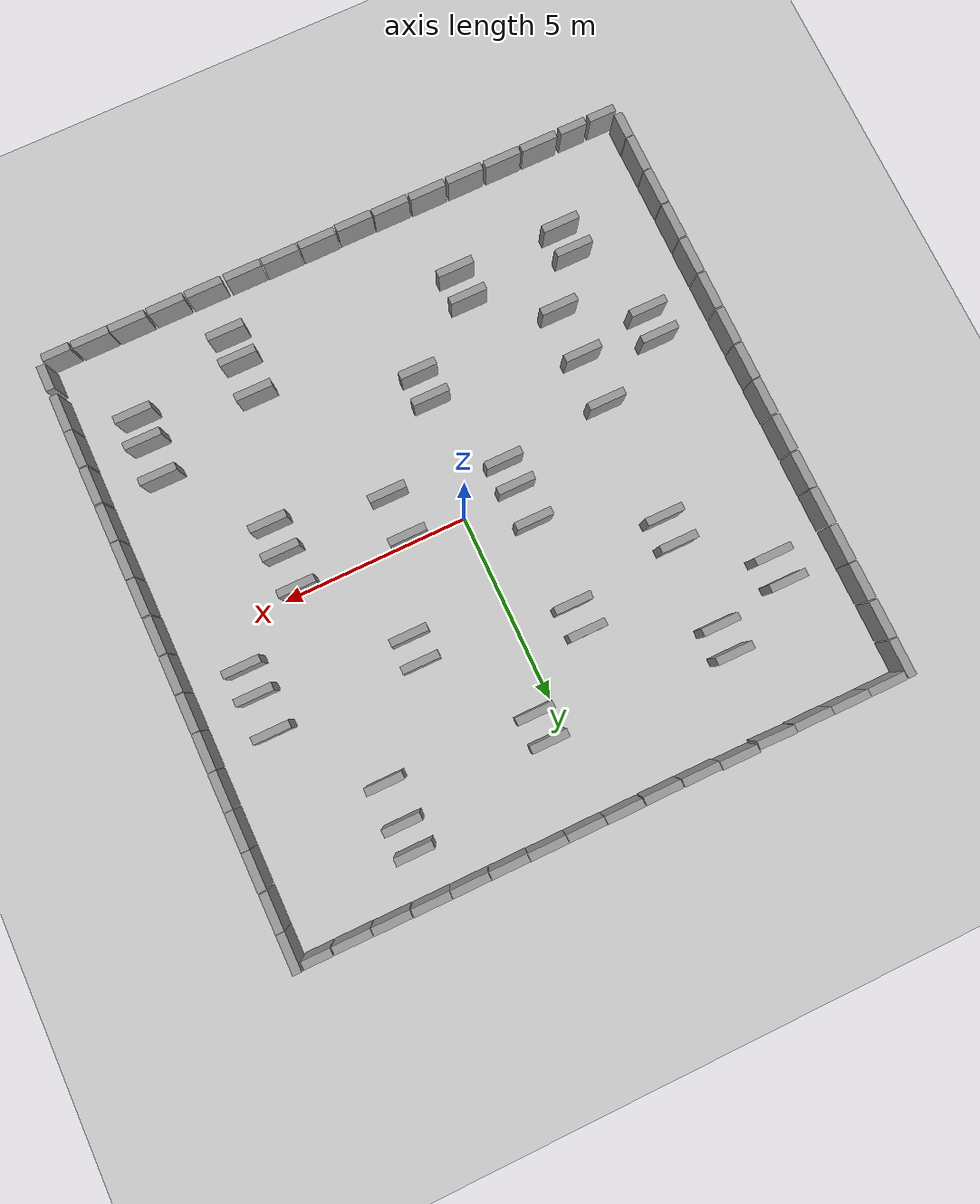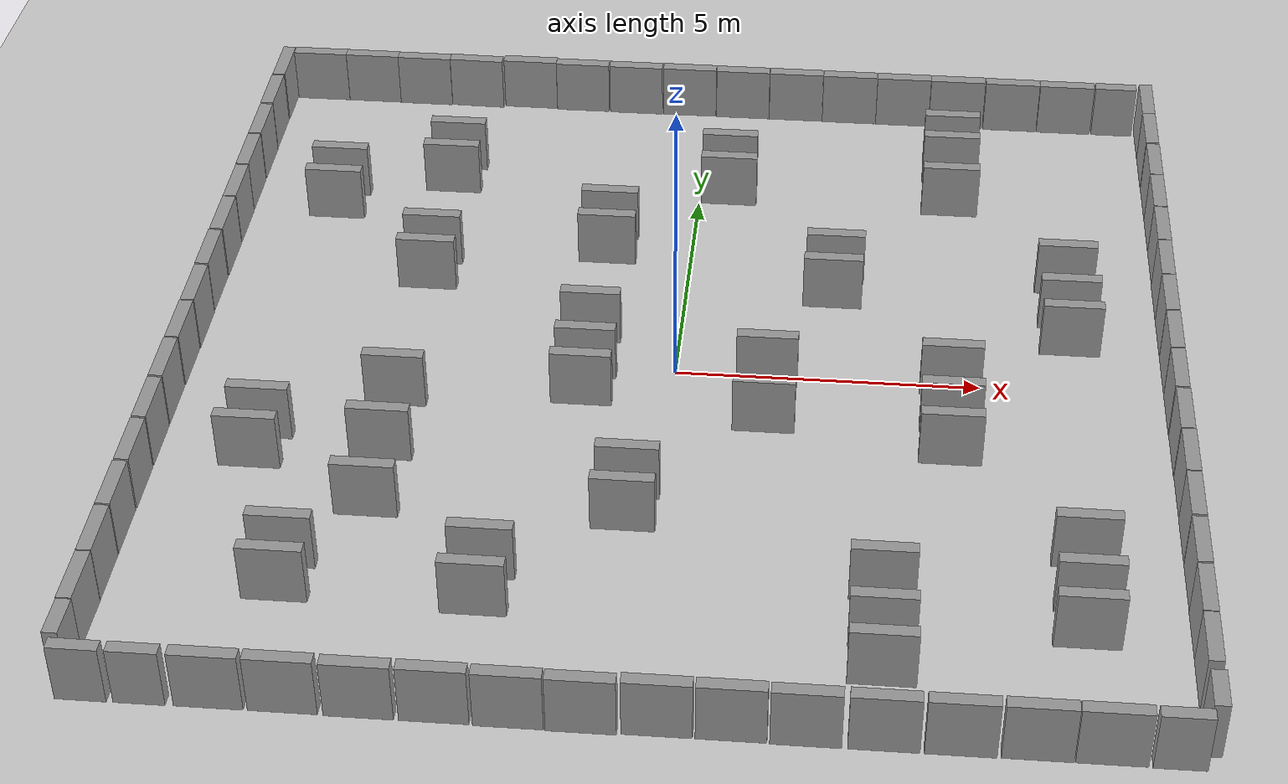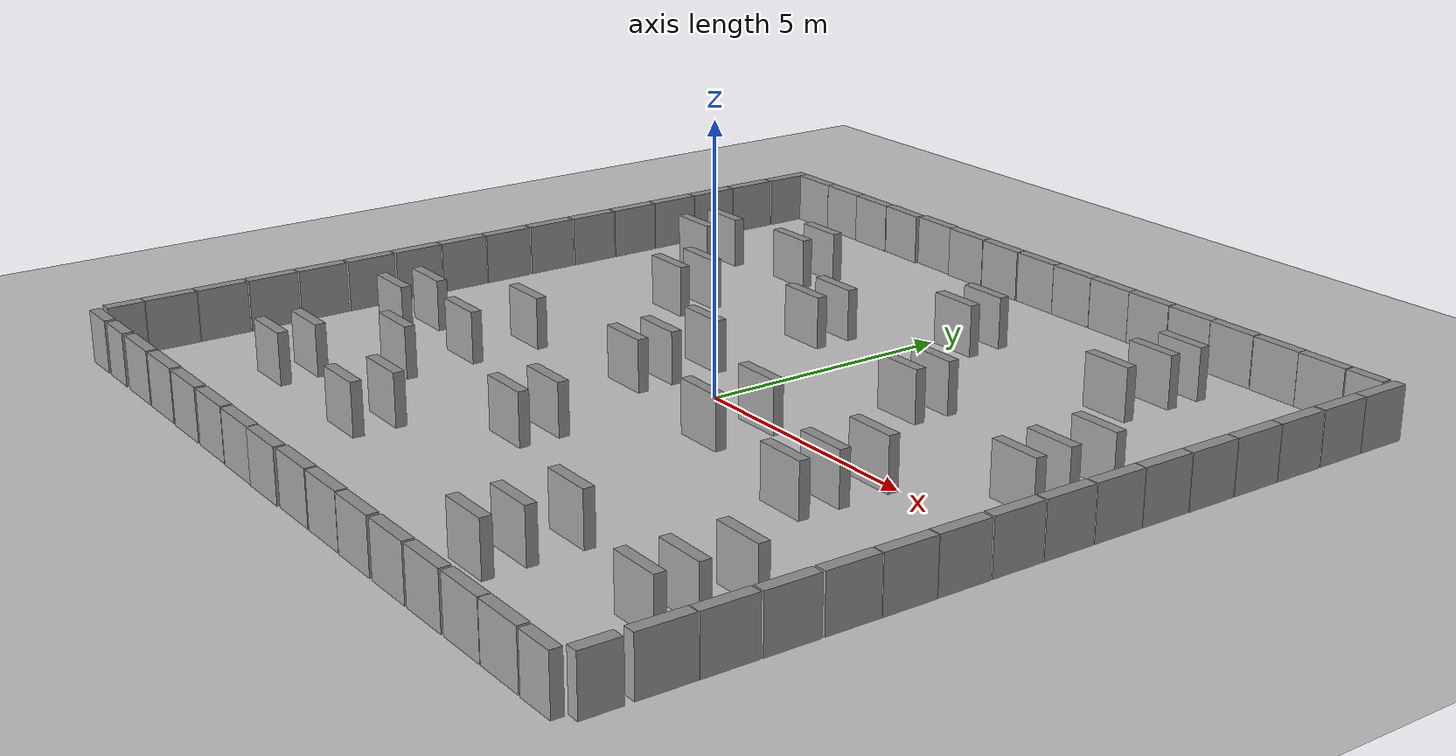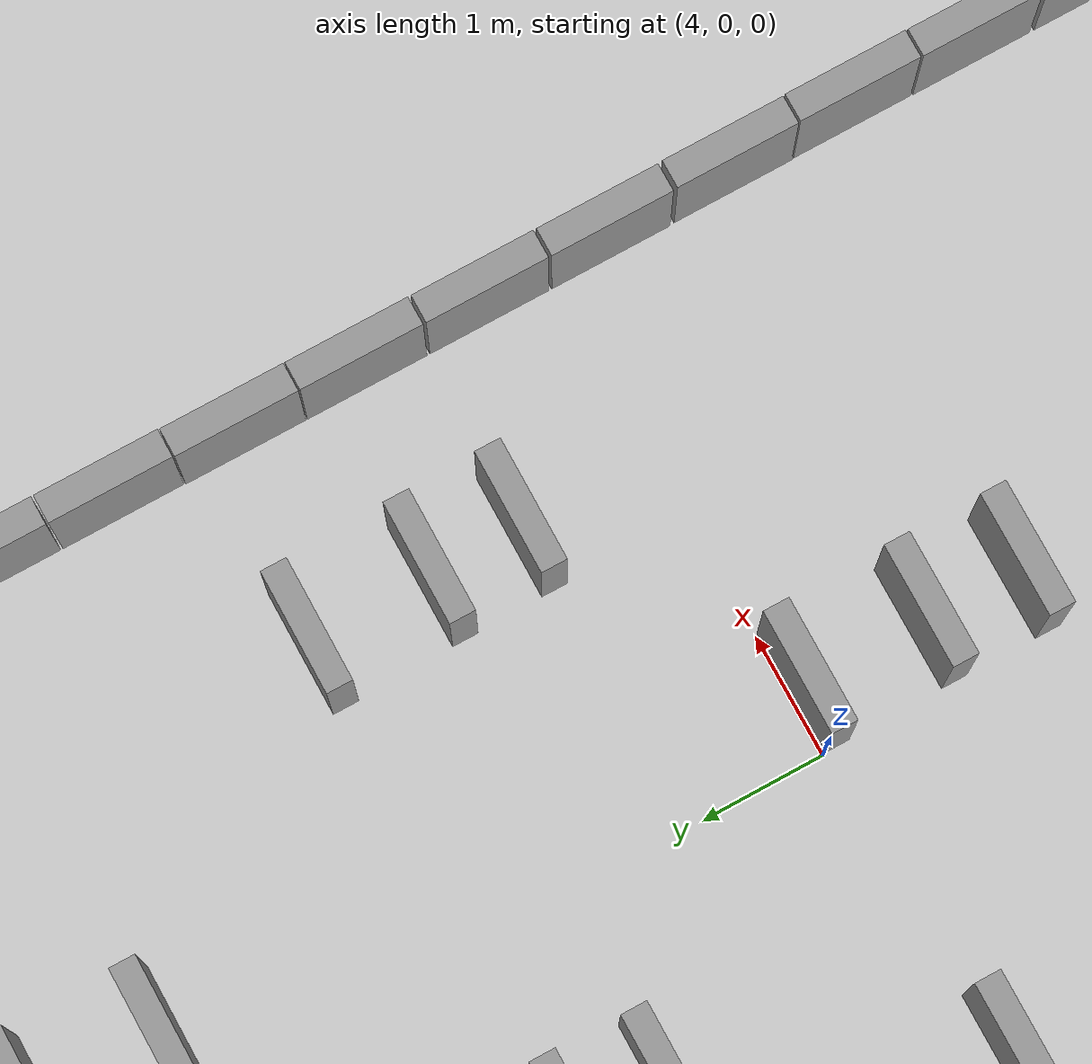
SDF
<sdf version="1.6">
 <world name="default">
  <light name="sun" type="directional">
   <pose>0 0 10 0 -0 0</pose>
   <diffuse>0.8 0.8 0.8 1</diffuse>
   <specular>0.1 0.1 0.1 1</specular>
   <attenuation>
    <range>1000</range>
    <constant>0.9</constant>
    <linear>0.01</linear>
    <quadratic>0.001</quadratic>
   </attenuation>
   <direction>-0.5 0.5 -1</direction>
  </light>
  <model name="ground_plane">
   <static>1</static>
   <static>1</static>
   <link name="link">
    <collision name="collision">
     <geometry><plane><normal>0 0 1</normal><size>100 100</size></plane></geometry>
     <surface><friction><ode><mu>100</mu><mu2>50</mu2></ode></friction></surface>
    </collision>
    <visual name="visual">
     <cast_shadows>0</cast_shadows>
     <geometry><plane><normal>0 0 1</normal><size>100 100</size></plane></geometry>
     <material>
      <script><uri>file://media/materials/scripts/gazebo.material</uri><name>Gazebo/Grey</name></script>
     </material>
    </visual>
   </link>
  </model>
  <gravity>0 0 -9.8</gravity>
  <magnetic_field>6e-06 2.3e-05 -4.2e-05</magnetic_field>
  <atmosphere type="adiabatic"/>
  <physics name="default_physics" default="0" type="ode">
   <max_step_size>0.001</max_step_size>
   <real_time_factor>1</real_time_factor>
   <real_time_update_rate>1000</real_time_update_rate>
  </physics>
  <scene><ambient>0.4 0.4 0.4 1</ambient><background>0.7 0.7 0.7 1</background><shadows>1</shadows></scene>
  <spherical_coordinates>
   <surface_model>EARTH_WGS84</surface_model>
   <latitude_deg>0</latitude_deg>
   <longitude_deg>0</longitude_deg>
   <elevation>0</elevation>
   <heading_deg>0</heading_deg>
  </spherical_coordinates>
  <audio><device>default</device></audio>
  <model name="unit_box_clone">
   <pose>-7.49845 8.12011 0.499999 1e-06 -2e-06 0.000156</pose>
   <link name="link">
    <inertial>
     <mass>1</mass>
     <inertia>
      <ixx>0.166667</ixx>
      <ixy>0</ixy>
      <ixz>0</ixz>
      <iyy>0.166667</iyy>
      <iyz>0</iyz>
      <izz>0.166667</izz>
     </inertia>
    </inertial>
    <collision name="collision"><geometry><box><size>1 0.210541 1</size></box></geometry></collision>
    <visual name="visual">
     <geometry><box><size>1 0.210541 1</size></box></geometry>
     <material>
      <script><name>Gazebo/Grey</name><uri>file://media/materials/scripts/gazebo.material</uri></script>
     </material>
    </visual>
   </link>
  </model>
  <model name="unit_box_clone_0">
   <pose>-6.4973 8.11973 0.500001 -8e-06 -0 -0.002301</pose>
   <link name="link">
    <inertial>
     <mass>1</mass>
     <inertia>
      <ixx>0.166667</ixx>
      <ixy>0</ixy>
      <ixz>0</ixz>
      <iyy>0.166667</iyy>
      <iyz>0</iyz>
      <izz>0.166667</izz>
     </inertia>
    </inertial>
    <collision name="collision"><geometry><box><size>1 0.210541 1</size></box></geometry></collision>
    <visual name="visual">
     <geometry><box><size>1 0.210541 1</size></box></geometry>
     <material>
      <script><name>Gazebo/Grey</name><uri>file://media/materials/scripts/gazebo.material</uri></script>
     </material>
    </visual>
   </link>
  </model>
  <model name="unit_box_clone_1">
   <pose>-5.49732 8.10848 0.499931 -0 -0 -0.002301</pose>
   <link name="link">
    <inertial>
     <mass>1</mass>
     <inertia>
      <ixx>0.166667</ixx>
      <ixy>0</ixy>
      <ixz>0</ixz>
      <iyy>0.166667</iyy>
      <iyz>0</iyz>
      <izz>0.166667</izz>
     </inertia>
    </inertial>
    <collision name="collision"><geometry><box><size>1 0.210541 1</size></box></geometry></collision>
    <visual name="visual">
     <geometry><box><size>1 0.210541 1</size></box></geometry>
     <material>
      <script><name>Gazebo/Grey</name><uri>file://media/materials/scripts/gazebo.material</uri></script>
     </material>
    </visual>
   </link>
  </model>
  <model name="unit_box_clone_2">
   <pose>-4.49485 8.11083 0.499999 1e-06 -2e-06 -0.026824</pose>
   <link name="link">
    <inertial>
     <mass>1</mass>
     <inertia>
      <ixx>0.166667</ixx>
      <ixy>0</ixy>
      <ixz>0</ixz>
      <iyy>0.166667</iyy>
      <iyz>0</iyz>
      <izz>0.166667</izz>
     </inertia>
    </inertial>
    <collision name="collision"><geometry><box><size>1 0.210541 1</size></box></geometry></collision>
    <visual name="visual">
     <geometry><box><size>1 0.210541 1</size></box></geometry>
     <material>
      <script><name>Gazebo/Grey</name><uri>file://media/materials/scripts/gazebo.material</uri></script>
     </material>
    </visual>
   </link>
  </model>
  <model name="unit_box_clone_3">
   <pose>-3.46835 8.14999 0.5 -0 -0 -0.007791</pose>
   <link name="link">
    <inertial>
     <mass>1</mass>
     <inertia>
      <ixx>0.166667</ixx>
      <ixy>0</ixy>
      <ixz>0</ixz>
      <iyy>0.166667</iyy>
      <iyz>0</iyz>
      <izz>0.166667</izz>
     </inertia>
    </inertial>
    <collision name="collision"><geometry><box><size>1 0.210541 1</size></box></geometry></collision>
    <visual name="visual">
     <geometry><box><size>1 0.210541 1</size></box></geometry>
     <material>
      <script><name>Gazebo/Grey</name><uri>file://media/materials/scripts/gazebo.material</uri></script>
     </material>
    </visual>
   </link>
  </model>
  <model name="unit_box_clone_4">
   <pose>-2.46316 8.1188 0.499999 1e-06 -2e-06 0.000156</pose>
   <link name="link">
    <inertial>
     <mass>1</mass>
     <inertia>
      <ixx>0.166667</ixx>
      <ixy>0</ixy>
      <ixz>0</ixz>
      <iyy>0.166667</iyy>
      <iyz>0</iyz>
      <izz>0.166667</izz>
     </inertia>
    </inertial>
    <collision name="collision"><geometry><box><size>1 0.210541 1</size></box></geometry></collision>
    <visual name="visual">
     <geometry><box><size>1 0.210541 1</size></box></geometry>
     <material>
      <script><name>Gazebo/Grey</name><uri>file://media/materials/scripts/gazebo.material</uri></script>
     </material>
    </visual>
   </link>
  </model>
  <model name="unit_box_clone_5">
   <pose>-1.44425 8.11214 0.499999 1e-06 -2e-06 0.000156</pose>
   <link name="link">
    <inertial>
     <mass>1</mass>
     <inertia>
      <ixx>0.166667</ixx>
      <ixy>0</ixy>
      <ixz>0</ixz>
      <iyy>0.166667</iyy>
      <iyz>0</iyz>
      <izz>0.166667</izz>
     </inertia>
    </inertial>
    <collision name="collision"><geometry><box><size>1 0.210541 1</size></box></geometry></collision>
    <visual name="visual">
     <geometry><box><size>1 0.210541 1</size></box></geometry>
     <material>
      <script><name>Gazebo/Grey</name><uri>file://media/materials/scripts/gazebo.material</uri></script>
     </material>
    </visual>
   </link>
  </model>
  <model name="unit_box_clone_6">
   <pose>-0.418685 8.11879 0.499999 1e-06 -2e-06 0.000156</pose>
   <link name="link">
    <inertial>
     <mass>1</mass>
     <inertia>
      <ixx>0.166667</ixx>
      <ixy>0</ixy>
      <ixz>0</ixz>
      <iyy>0.166667</iyy>
      <iyz>0</iyz>
      <izz>0.166667</izz>
     </inertia>
    </inertial>
    <collision name="collision"><geometry><box><size>1 0.210541 1</size></box></geometry></collision>
    <visual name="visual">
     <geometry><box><size>1 0.210541 1</size></box></geometry>
     <material>
      <script><name>Gazebo/Grey</name><uri>file://media/materials/scripts/gazebo.material</uri></script>
     </material>
    </visual>
   </link>
  </model>
  <model name="unit_box_clone_7">
   <pose>0.592834 8.11166 0.499999 1e-06 -2e-06 0.000156</pose>
   <link name="link">
    <inertial>
     <mass>1</mass>
     <inertia>
      <ixx>0.166667</ixx>
      <ixy>0</ixy>
      <ixz>0</ixz>
      <iyy>0.166667</iyy>
      <iyz>0</iyz>
      <izz>0.166667</izz>
     </inertia>
    </inertial>
    <collision name="collision"><geometry><box><size>1 0.210541 1</size></box></geometry></collision>
    <visual name="visual">
     <geometry><box><size>1 0.210541 1</size></box></geometry>
     <material>
      <script><name>Gazebo/Grey</name><uri>file://media/materials/scripts/gazebo.material</uri></script>
     </material>
    </visual>
   </link>
  </model>
  <model name="unit_box_clone_8">
   <pose>1.60043 8.11017 0.499999 1e-06 -2e-06 0.000156</pose>
   <link name="link">
    <inertial>
     <mass>1</mass>
     <inertia>
      <ixx>0.166667</ixx>
      <ixy>0</ixy>
      <ixz>0</ixz>
      <iyy>0.166667</iyy>
      <iyz>0</iyz>
      <izz>0.166667</izz>
     </inertia>
    </inertial>
    <collision name="collision"><geometry><box><size>1 0.210541 1</size></box></geometry></collision>
    <visual name="visual">
     <geometry><box><size>1 0.210541 1</size></box></geometry>
     <material>
      <script><name>Gazebo/Grey</name><uri>file://media/materials/scripts/gazebo.material</uri></script>
     </material>
    </visual>
   </link>
  </model>
  <model name="unit_box_clone_9">
   <pose>2.60987 8.10298 0.499999 1e-06 -2e-06 0.000156</pose>
   <link name="link">
    <inertial>
     <mass>1</mass>
     <inertia>
      <ixx>0.166667</ixx>
      <ixy>0</ixy>
      <ixz>0</ixz>
      <iyy>0.166667</iyy>
      <iyz>0</iyz>
      <izz>0.166667</izz>
     </inertia>
    </inertial>
    <collision name="collision"><geometry><box><size>1 0.210541 1</size></box></geometry></collision>
    <visual name="visual">
     <geometry><box><size>1 0.210541 1</size></box></geometry>
     <material>
      <script><name>Gazebo/Grey</name><uri>file://media/materials/scripts/gazebo.material</uri></script>
     </material>
    </visual>
   </link>
  </model>
  <model name="unit_box_clone_10">
   <pose>3.62649 8.09939 0.499999 1e-06 -2e-06 0.000156</pose>
   <link name="link">
    <inertial>
     <mass>1</mass>
     <inertia>
      <ixx>0.166667</ixx>
      <ixy>0</ixy>
      <ixz>0</ixz>
      <iyy>0.166667</iyy>
      <iyz>0</iyz>
      <izz>0.166667</izz>
     </inertia>
    </inertial>
    <collision name="collision"><geometry><box><size>1 0.210541 1</size></box></geometry></collision>
    <visual name="visual">
     <geometry><box><size>1 0.210541 1</size></box></geometry>
     <material>
      <script><name>Gazebo/Grey</name><uri>file://media/materials/scripts/gazebo.material</uri></script>
     </material>
    </visual>
   </link>
  </model>
  <model name="unit_box_clone_11">
   <pose>4.63311 8.09523 0.5 0 -0 -0.003214</pose>
   <link name="link">
    <inertial>
     <mass>1</mass>
     <inertia>
      <ixx>0.166667</ixx>
      <ixy>0</ixy>
      <ixz>0</ixz>
      <iyy>0.166667</iyy>
      <iyz>0</iyz>
      <izz>0.166667</izz>
     </inertia>
    </inertial>
    <collision name="collision"><geometry><box><size>1 0.210541 1</size></box></geometry></collision>
    <visual name="visual">
     <geometry><box><size>1 0.210541 1</size></box></geometry>
     <material>
      <script><name>Gazebo/Grey</name><uri>file://media/materials/scripts/gazebo.material</uri></script>
     </material>
    </visual>
   </link>
  </model>
  <model name="unit_box_0_clone_0">
   <pose>8.11522 6.68459 0.5 0 0 -0.00024</pose>
   <link name="link">
    <inertial>
     <mass>1</mass>
     <inertia>
      <ixx>0.166667</ixx>
      <ixy>0</ixy>
      <ixz>0</ixz>
      <iyy>0.166667</iyy>
      <iyz>0</iyz>
      <izz>0.166667</izz>
     </inertia>
    </inertial>
    <collision name="collision"><geometry><box><size>0.230819 1 1</size></box></geometry></collision>
    <visual name="visual">
     <geometry><box><size>0.230819 1 1</size></box></geometry>
     <material>
      <script><name>Gazebo/Grey</name><uri>file://media/materials/scripts/gazebo.material</uri></script>
     </material>
    </visual>
   </link>
  </model>
  <model name="unit_box_0_clone_1">
   <pose>8.11915 5.6517 0.5 1e-06 1e-06 0.000156</pose>
   <link name="link">
    <inertial>
     <mass>1</mass>
     <inertia>
      <ixx>0.166667</ixx>
      <ixy>0</ixy>
      <ixz>0</ixz>
      <iyy>0.166667</iyy>
      <iyz>0</iyz>
      <izz>0.166667</izz>
     </inertia>
    </inertial>
    <collision name="collision"><geometry><box><size>0.230819 1 1</size></box></geometry></collision>
    <visual name="visual">
     <geometry><box><size>0.230819 1 1</size></box></geometry>
     <material>
      <script><name>Gazebo/Grey</name><uri>file://media/materials/scripts/gazebo.material</uri></script>
     </material>
    </visual>
   </link>
  </model>
  <model name="unit_box_0_clone_2">
   <pose>8.11914 4.64016 0.5 1e-06 1e-06 0.00025</pose>
   <link name="link">
    <inertial>
     <mass>1</mass>
     <inertia>
      <ixx>0.166667</ixx>
      <ixy>0</ixy>
      <ixz>0</ixz>
      <iyy>0.166667</iyy>
      <iyz>0</iyz>
      <izz>0.166667</izz>
     </inertia>
    </inertial>
    <collision name="collision"><geometry><box><size>0.230819 1 1</size></box></geometry></collision>
    <visual name="visual">
     <geometry><box><size>0.230819 1 1</size></box></geometry>
     <material>
      <script><name>Gazebo/Grey</name><uri>file://media/materials/scripts/gazebo.material</uri></script>
     </material>
    </visual>
   </link>
  </model>
  <model name="unit_box_0_clone_3">
   <pose>8.11914 3.62227 0.5 1e-06 1e-06 0.000231</pose>
   <link name="link">
    <inertial>
     <mass>1</mass>
     <inertia>
      <ixx>0.166667</ixx>
      <ixy>0</ixy>
      <ixz>0</ixz>
      <iyy>0.166667</iyy>
      <iyz>0</iyz>
      <izz>0.166667</izz>
     </inertia>
    </inertial>
    <collision name="collision"><geometry><box><size>0.230819 1 1</size></box></geometry></collision>
    <visual name="visual">
     <geometry><box><size>0.230819 1 1</size></box></geometry>
     <material>
      <script><name>Gazebo/Grey</name><uri>file://media/materials/scripts/gazebo.material</uri></script>
     </material>
    </visual>
   </link>
  </model>
  <model name="unit_box_0_clone_4">
   <pose>8.11332 2.61062 0.5 1e-06 1e-06 -0.001006</pose>
   <link name="link">
    <inertial>
     <mass>1</mass>
     <inertia>
      <ixx>0.166667</ixx>
      <ixy>0</ixy>
      <ixz>0</ixz>
      <iyy>0.166667</iyy>
      <iyz>0</iyz>
      <izz>0.166667</izz>
     </inertia>
    </inertial>
    <collision name="collision"><geometry><box><size>0.230819 1 1</size></box></geometry></collision>
    <visual name="visual">
     <geometry><box><size>0.230819 1 1</size></box></geometry>
     <material>
      <script><name>Gazebo/Grey</name><uri>file://media/materials/scripts/gazebo.material</uri></script>
     </material>
    </visual>
   </link>
  </model>
  <model name="unit_box_0_clone_5">
   <pose>8.11277 1.59919 0.5 1e-06 1e-06 0.000231</pose>
   <link name="link">
    <inertial>
     <mass>1</mass>
     <inertia>
      <ixx>0.166667</ixx>
      <ixy>0</ixy>
      <ixz>0</ixz>
      <iyy>0.166667</iyy>
      <iyz>0</iyz>
      <izz>0.166667</izz>
     </inertia>
    </inertial>
    <collision name="collision"><geometry><box><size>0.230819 1 1</size></box></geometry></collision>
    <visual name="visual">
     <geometry><box><size>0.230819 1 1</size></box></geometry>
     <material>
      <script><name>Gazebo/Grey</name><uri>file://media/materials/scripts/gazebo.material</uri></script>
     </material>
    </visual>
   </link>
  </model>
  <model name="unit_box_0_clone_6">
   <pose>8.11277 0.574937 0.5 1e-06 1e-06 0.000231</pose>
   <link name="link">
    <inertial>
     <mass>1</mass>
     <inertia>
      <ixx>0.166667</ixx>
      <ixy>0</ixy>
      <ixz>0</ixz>
      <iyy>0.166667</iyy>
      <iyz>0</iyz>
      <izz>0.166667</izz>
     </inertia>
    </inertial>
    <collision name="collision"><geometry><box><size>0.230819 1 1</size></box></geometry></collision>
    <visual name="visual">
     <geometry><box><size>0.230819 1 1</size></box></geometry>
     <material>
      <script><name>Gazebo/Grey</name><uri>file://media/materials/scripts/gazebo.material</uri></script>
     </material>
    </visual>
   </link>
  </model>
  <model name="unit_box_0_clone_7">
   <pose>8.11276 -0.449321 0.5 1e-06 1e-06 0.000231</pose>
   <link name="link">
    <inertial>
     <mass>1</mass>
     <inertia>
      <ixx>0.166667</ixx>
      <ixy>0</ixy>
      <ixz>0</ixz>
      <iyy>0.166667</iyy>
      <iyz>0</iyz>
      <izz>0.166667</izz>
     </inertia>
    </inertial>
    <collision name="collision"><geometry><box><size>0.230819 1 1</size></box></geometry></collision>
    <visual name="visual">
     <geometry><box><size>0.230819 1 1</size></box></geometry>
     <material>
      <script><name>Gazebo/Grey</name><uri>file://media/materials/scripts/gazebo.material</uri></script>
     </material>
    </visual>
   </link>
  </model>
  <model name="unit_box_0_clone_8">
   <pose>8.11912 -1.4863 0.5 1e-06 1e-06 0.000231</pose>
   <link name="link">
    <inertial>
     <mass>1</mass>
     <inertia>
      <ixx>0.166667</ixx>
      <ixy>0</ixy>
      <ixz>0</ixz>
      <iyy>0.166667</iyy>
      <iyz>0</iyz>
      <izz>0.166667</izz>
     </inertia>
    </inertial>
    <collision name="collision"><geometry><box><size>0.230819 1 1</size></box></geometry></collision>
    <visual name="visual">
     <geometry><box><size>0.230819 1 1</size></box></geometry>
     <material>
      <script><name>Gazebo/Grey</name><uri>file://media/materials/scripts/gazebo.material</uri></script>
     </material>
    </visual>
   </link>
  </model>
  <model name="unit_box_0_clone_9">
   <pose>8.12548 -2.5042 0.5 1e-06 1e-06 0.000231</pose>
   <link name="link">
    <inertial>
     <mass>1</mass>
     <inertia>
      <ixx>0.166667</ixx>
      <ixy>0</ixy>
      <ixz>0</ixz>
      <iyy>0.166667</iyy>
      <iyz>0</iyz>
      <izz>0.166667</izz>
     </inertia>
    </inertial>
    <collision name="collision"><geometry><box><size>0.230819 1 1</size></box></geometry></collision>
    <visual name="visual">
     <geometry><box><size>0.230819 1 1</size></box></geometry>
     <material>
      <script><name>Gazebo/Grey</name><uri>file://media/materials/scripts/gazebo.material</uri></script>
     </material>
    </visual>
   </link>
  </model>
  <model name="unit_box_0_clone_10">
   <pose>8.12331 -3.52223 0.5 1e-06 1e-06 0.000231</pose>
   <link name="link">
    <inertial>
     <mass>1</mass>
     <inertia>
      <ixx>0.166667</ixx>
      <ixy>0</ixy>
      <ixz>0</ixz>
      <iyy>0.166667</iyy>
      <iyz>0</iyz>
      <izz>0.166667</izz>
     </inertia>
    </inertial>
    <collision name="collision"><geometry><box><size>0.230819 1 1</size></box></geometry></collision>
    <visual name="visual">
     <geometry><box><size>0.230819 1 1</size></box></geometry>
     <material>
      <script><name>Gazebo/Grey</name><uri>file://media/materials/scripts/gazebo.material</uri></script>
     </material>
    </visual>
   </link>
  </model>
  <model name="unit_box_0_clone_11">
   <pose>8.1233 -4.56316 0.5 1e-06 1e-06 0.000231</pose>
   <link name="link">
    <inertial>
     <mass>1</mass>
     <inertia>
      <ixx>0.166667</ixx>
      <ixy>0</ixy>
      <ixz>0</ixz>
      <iyy>0.166667</iyy>
      <iyz>0</iyz>
      <izz>0.166667</izz>
     </inertia>
    </inertial>
    <collision name="collision"><geometry><box><size>0.230819 1 1</size></box></geometry></collision>
    <visual name="visual">
     <geometry><box><size>0.230819 1 1</size></box></geometry>
     <material>
      <script><name>Gazebo/Grey</name><uri>file://media/materials/scripts/gazebo.material</uri></script>
     </material>
    </visual>
   </link>
  </model>
  <model name="unit_box_0_clone_12">
   <pose>8.11815 -5.59377 0.5 1e-06 1e-06 0.000231</pose>
   <link name="link">
    <inertial>
     <mass>1</mass>
     <inertia>
      <ixx>0.166667</ixx>
      <ixy>0</ixy>
      <ixz>0</ixz>
      <iyy>0.166667</iyy>
      <iyz>0</iyz>
      <izz>0.166667</izz>
     </inertia>
    </inertial>
    <collision name="collision"><geometry><box><size>0.230819 1 1</size></box></geometry></collision>
    <visual name="visual">
     <geometry><box><size>0.230819 1 1</size></box></geometry>
     <material>
      <script><name>Gazebo/Grey</name><uri>file://media/materials/scripts/gazebo.material</uri></script>
     </material>
    </visual>
   </link>
  </model>
  <model name="unit_box_0_clone_13">
   <pose>8.11333 -6.60776 0.5 1e-06 1e-06 -0.005436</pose>
   <link name="link">
    <inertial>
     <mass>1</mass>
     <inertia>
      <ixx>0.166667</ixx>
      <ixy>0</ixy>
      <ixz>0</ixz>
      <iyy>0.166667</iyy>
      <iyz>0</iyz>
      <izz>0.166667</izz>
     </inertia>
    </inertial>
    <collision name="collision"><geometry><box><size>0.230819 1 1</size></box></geometry></collision>
    <visual name="visual">
     <geometry><box><size>0.230819 1 1</size></box></geometry>
     <material>
      <script><name>Gazebo/Grey</name><uri>file://media/materials/scripts/gazebo.material</uri></script>
     </material>
    </visual>
   </link>
  </model>
  <model name="unit_box_clone_15_clone_0">
   <pose>6.71207 -8.13093 0.499999 1e-06 -2e-06 0.000156</pose>
   <link name="link">
    <inertial>
     <mass>1</mass>
     <inertia>
      <ixx>0.166667</ixx>
      <ixy>0</ixy>
      <ixz>0</ixz>
      <iyy>0.166667</iyy>
      <iyz>0</iyz>
      <izz>0.166667</izz>
     </inertia>
    </inertial>
    <collision name="collision"><geometry><box><size>1 0.210541 1</size></box></geometry></collision>
    <visual name="visual">
     <geometry><box><size>1 0.210541 1</size></box></geometry>
     <material>
      <script><name>Gazebo/Grey</name><uri>file://media/materials/scripts/gazebo.material</uri></script>
     </material>
    </visual>
   </link>
  </model>
  <model name="unit_box_clone_15_clone_1">
   <pose>5.69715 -8.13092 0.499999 1e-06 -2e-06 0.000156</pose>
   <link name="link">
    <inertial>
     <mass>1</mass>
     <inertia>
      <ixx>0.166667</ixx>
      <ixy>0</ixy>
      <ixz>0</ixz>
      <iyy>0.166667</iyy>
      <iyz>0</iyz>
      <izz>0.166667</izz>
     </inertia>
    </inertial>
    <collision name="collision"><geometry><box><size>1 0.210541 1</size></box></geometry></collision>
    <visual name="visual">
     <geometry><box><size>1 0.210541 1</size></box></geometry>
     <material>
      <script><name>Gazebo/Grey</name><uri>file://media/materials/scripts/gazebo.material</uri></script>
     </material>
    </visual>
   </link>
  </model>
  <model name="unit_box_clone_15_clone_2">
   <pose>4.63881 -8.1371 0.499999 1e-06 -2e-06 0.000156</pose>
   <link name="link">
    <inertial>
     <mass>1</mass>
     <inertia>
      <ixx>0.166667</ixx>
      <ixy>0</ixy>
      <ixz>0</ixz>
      <iyy>0.166667</iyy>
      <iyz>0</iyz>
      <izz>0.166667</izz>
     </inertia>
    </inertial>
    <collision name="collision"><geometry><box><size>1 0.210541 1</size></box></geometry></collision>
    <visual name="visual">
     <geometry><box><size>1 0.210541 1</size></box></geometry>
     <material>
      <script><name>Gazebo/Grey</name><uri>file://media/materials/scripts/gazebo.material</uri></script>
     </material>
    </visual>
   </link>
  </model>
  <model name="unit_box_clone_15_clone_3">
   <pose>3.57975 -8.1371 0.499999 1e-06 -2e-06 0.000156</pose>
   <link name="link">
    <inertial>
     <mass>1</mass>
     <inertia>
      <ixx>0.166667</ixx>
      <ixy>0</ixy>
      <ixz>0</ixz>
      <iyy>0.166667</iyy>
      <iyz>0</iyz>
      <izz>0.166667</izz>
     </inertia>
    </inertial>
    <collision name="collision"><geometry><box><size>1 0.210541 1</size></box></geometry></collision>
    <visual name="visual">
     <geometry><box><size>1 0.210541 1</size></box></geometry>
     <material>
      <script><name>Gazebo/Grey</name><uri>file://media/materials/scripts/gazebo.material</uri></script>
     </material>
    </visual>
   </link>
  </model>
  <model name="unit_box_clone_15_clone_4">
   <pose>2.49815 -8.13709 0.499999 1e-06 -2e-06 0.000156</pose>
   <link name="link">
    <inertial>
     <mass>1</mass>
     <inertia>
      <ixx>0.166667</ixx>
      <ixy>0</ixy>
      <ixz>0</ixz>
      <iyy>0.166667</iyy>
      <iyz>0</iyz>
      <izz>0.166667</izz>
     </inertia>
    </inertial>
    <collision name="collision"><geometry><box><size>1 0.210541 1</size></box></geometry></collision>
    <visual name="visual">
     <geometry><box><size>1 0.210541 1</size></box></geometry>
     <material>
      <script><name>Gazebo/Grey</name><uri>file://media/materials/scripts/gazebo.material</uri></script>
     </material>
    </visual>
   </link>
  </model>
  <model name="unit_box_clone_15_clone_5">
   <pose>1.46162 -8.12582 0.499999 1e-06 -2e-06 0.000156</pose>
   <link name="link">
    <inertial>
     <mass>1</mass>
     <inertia>
      <ixx>0.166667</ixx>
      <ixy>0</ixy>
      <ixz>0</ixz>
      <iyy>0.166667</iyy>
      <iyz>0</iyz>
      <izz>0.166667</izz>
     </inertia>
    </inertial>
    <collision name="collision"><geometry><box><size>1 0.210541 1</size></box></geometry></collision>
    <visual name="visual">
     <geometry><box><size>1 0.210541 1</size></box></geometry>
     <material>
      <script><name>Gazebo/Grey</name><uri>file://media/materials/scripts/gazebo.material</uri></script>
     </material>
    </visual>
   </link>
  </model>
  <model name="unit_box_clone_15_clone_6">
   <pose>0.425087 -8.12581 0.499999 1e-06 -2e-06 0.000156</pose>
   <link name="link">
    <inertial>
     <mass>1</mass>
     <inertia>
      <ixx>0.166667</ixx>
      <ixy>0</ixy>
      <ixz>0</ixz>
      <iyy>0.166667</iyy>
      <iyz>0</iyz>
      <izz>0.166667</izz>
     </inertia>
    </inertial>
    <collision name="collision"><geometry><box><size>1 0.210541 1</size></box></geometry></collision>
    <visual name="visual">
     <geometry><box><size>1 0.210541 1</size></box></geometry>
     <material>
      <script><name>Gazebo/Grey</name><uri>file://media/materials/scripts/gazebo.material</uri></script>
     </material>
    </visual>
   </link>
  </model>
  <model name="unit_box_clone_15_clone_7">
   <pose>-0.633975 -8.14836 0.499999 1e-06 -2e-06 0.000156</pose>
   <link name="link">
    <inertial>
     <mass>1</mass>
     <inertia>
      <ixx>0.166667</ixx>
      <ixy>0</ixy>
      <ixz>0</ixz>
      <iyy>0.166667</iyy>
      <iyz>0</iyz>
      <izz>0.166667</izz>
     </inertia>
    </inertial>
    <collision name="collision"><geometry><box><size>1 0.210541 1</size></box></geometry></collision>
    <visual name="visual">
     <geometry><box><size>1 0.210541 1</size></box></geometry>
     <material>
      <script><name>Gazebo/Grey</name><uri>file://media/materials/scripts/gazebo.material</uri></script>
     </material>
    </visual>
   </link>
  </model>
  <model name="unit_box_clone_15_clone_8">
   <pose>-1.65923 -8.13708 0.499999 1e-06 -2e-06 0.000156</pose>
   <link name="link">
    <inertial>
     <mass>1</mass>
     <inertia>
      <ixx>0.166667</ixx>
      <ixy>0</ixy>
      <ixz>0</ixz>
      <iyy>0.166667</iyy>
      <iyz>0</iyz>
      <izz>0.166667</izz>
     </inertia>
    </inertial>
    <collision name="collision"><geometry><box><size>1 0.210541 1</size></box></geometry></collision>
    <visual name="visual">
     <geometry><box><size>1 0.210541 1</size></box></geometry>
     <material>
      <script><name>Gazebo/Grey</name><uri>file://media/materials/scripts/gazebo.material</uri></script>
     </material>
    </visual>
   </link>
  </model>
  <model name="unit_box_clone_15_clone_9">
   <pose>-2.70703 -8.12583 0.499999 1e-06 -2e-06 0.000156</pose>
   <link name="link">
    <inertial>
     <mass>1</mass>
     <inertia>
      <ixx>0.166667</ixx>
      <ixy>0</ixy>
      <ixz>0</ixz>
      <iyy>0.166667</iyy>
      <iyz>0</iyz>
      <izz>0.166667</izz>
     </inertia>
    </inertial>
    <collision name="collision"><geometry><box><size>1 0.210541 1</size></box></geometry></collision>
    <visual name="visual">
     <geometry><box><size>1 0.210541 1</size></box></geometry>
     <material>
      <script><name>Gazebo/Grey</name><uri>file://media/materials/scripts/gazebo.material</uri></script>
     </material>
    </visual>
   </link>
  </model>
  <model name="unit_box_clone_15_clone_10">
   <pose>-3.77736 -8.12582 0.499999 1e-06 -2e-06 0.000156</pose>
   <link name="link">
    <inertial>
     <mass>1</mass>
     <inertia>
      <ixx>0.166667</ixx>
      <ixy>0</ixy>
      <ixz>0</ixz>
      <iyy>0.166667</iyy>
      <iyz>0</iyz>
      <izz>0.166667</izz>
     </inertia>
    </inertial>
    <collision name="collision"><geometry><box><size>1 0.210541 1</size></box></geometry></collision>
    <visual name="visual">
     <geometry><box><size>1 0.210541 1</size></box></geometry>
     <material>
      <script><name>Gazebo/Grey</name><uri>file://media/materials/scripts/gazebo.material</uri></script>
     </material>
    </visual>
   </link>
  </model>
  <model name="unit_box_clone_15_clone_11">
   <pose>-4.85896 -8.11456 0.499999 1e-06 -2e-06 0.000156</pose>
   <link name="link">
    <inertial>
     <mass>1</mass>
     <inertia>
      <ixx>0.166667</ixx>
      <ixy>0</ixy>
      <ixz>0</ixz>
      <iyy>0.166667</iyy>
      <iyz>0</iyz>
      <izz>0.166667</izz>
     </inertia>
    </inertial>
    <collision name="collision"><geometry><box><size>1 0.210541 1</size></box></geometry></collision>
    <visual name="visual">
     <geometry><box><size>1 0.210541 1</size></box></geometry>
     <material>
      <script><name>Gazebo/Grey</name><uri>file://media/materials/scripts/gazebo.material</uri></script>
     </material>
    </visual>
   </link>
  </model>
  <model name="unit_box_clone_15_clone_12">
   <pose>-5.91802 -8.11455 0.499999 1e-06 -2e-06 0.000156</pose>
   <link name="link">
    <inertial>
     <mass>1</mass>
     <inertia>
      <ixx>0.166667</ixx>
      <ixy>0</ixy>
      <ixz>0</ixz>
      <iyy>0.166667</iyy>
      <iyz>0</iyz>
      <izz>0.166667</izz>
     </inertia>
    </inertial>
    <collision name="collision"><geometry><box><size>1 0.210541 1</size></box></geometry></collision>
    <visual name="visual">
     <geometry><box><size>1 0.210541 1</size></box></geometry>
     <material>
      <script><name>Gazebo/Grey</name><uri>file://media/materials/scripts/gazebo.material</uri></script>
     </material>
    </visual>
   </link>
  </model>
  <model name="unit_box_0_clone_4_clone">
   <pose>-8.12647 7.71769 0.5 1e-06 1e-06 0.000231</pose>
   <link name="link">
    <inertial>
     <mass>1</mass>
     <inertia>
      <ixx>0.166667</ixx>
      <ixy>0</ixy>
      <ixz>0</ixz>
      <iyy>0.166667</iyy>
      <iyz>0</iyz>
      <izz>0.166667</izz>
     </inertia>
    </inertial>
    <collision name="collision"><geometry><box><size>0.230819 1 1</size></box></geometry></collision>
    <visual name="visual">
     <geometry><box><size>0.230819 1 1</size></box></geometry>
     <material>
      <script><name>Gazebo/Grey</name><uri>file://media/materials/scripts/gazebo.material</uri></script>
     </material>
    </visual>
   </link>
  </model>
  <model name="unit_box_0_clone_4_clone_0">
   <pose>-8.13281 6.68715 0.5 1e-06 1e-06 0.000231</pose>
   <link name="link">
    <inertial>
     <mass>1</mass>
     <inertia>
      <ixx>0.166667</ixx>
      <ixy>0</ixy>
      <ixz>0</ixz>
      <iyy>0.166667</iyy>
      <iyz>0</iyz>
      <izz>0.166667</izz>
     </inertia>
    </inertial>
    <collision name="collision"><geometry><box><size>0.230819 1 1</size></box></geometry></collision>
    <visual name="visual">
     <geometry><box><size>0.230819 1 1</size></box></geometry>
     <material>
      <script><name>Gazebo/Grey</name><uri>file://media/materials/scripts/gazebo.material</uri></script>
     </material>
    </visual>
   </link>
  </model>
  <model name="unit_box_0_clone_4_clone_1">
   <pose>-8.12606 5.64722 0.5 1e-06 1e-06 0.000231</pose>
   <link name="link">
    <inertial>
     <mass>1</mass>
     <inertia>
      <ixx>0.166667</ixx>
      <ixy>0</ixy>
      <ixz>0</ixz>
      <iyy>0.166667</iyy>
      <iyz>0</iyz>
      <izz>0.166667</izz>
     </inertia>
    </inertial>
    <collision name="collision"><geometry><box><size>0.230819 1 1</size></box></geometry></collision>
    <visual name="visual">
     <geometry><box><size>0.230819 1 1</size></box></geometry>
     <material>
      <script><name>Gazebo/Grey</name><uri>file://media/materials/scripts/gazebo.material</uri></script>
     </material>
    </visual>
   </link>
  </model>
  <model name="unit_box_0_clone_4_clone_2">
   <pose>-8.12607 4.6208 0.5 1e-06 1e-06 0.000231</pose>
   <link name="link">
    <inertial>
     <mass>1</mass>
     <inertia>
      <ixx>0.166667</ixx>
      <ixy>0</ixy>
      <ixz>0</ixz>
      <iyy>0.166667</iyy>
      <iyz>0</iyz>
      <izz>0.166667</izz>
     </inertia>
    </inertial>
    <collision name="collision"><geometry><box><size>0.230819 1 1</size></box></geometry></collision>
    <visual name="visual">
     <geometry><box><size>0.230819 1 1</size></box></geometry>
     <material>
      <script><name>Gazebo/Grey</name><uri>file://media/materials/scripts/gazebo.material</uri></script>
     </material>
    </visual>
   </link>
  </model>
  <model name="unit_box_0_clone_4_clone_3">
   <pose>-8.11932 3.59438 0.5 1e-06 1e-06 0.000231</pose>
   <link name="link">
    <inertial>
     <mass>1</mass>
     <inertia>
      <ixx>0.166667</ixx>
      <ixy>0</ixy>
      <ixz>0</ixz>
      <iyy>0.166667</iyy>
      <iyz>0</iyz>
      <izz>0.166667</izz>
     </inertia>
    </inertial>
    <collision name="collision"><geometry><box><size>0.230819 1 1</size></box></geometry></collision>
    <visual name="visual">
     <geometry><box><size>0.230819 1 1</size></box></geometry>
     <material>
      <script><name>Gazebo/Grey</name><uri>file://media/materials/scripts/gazebo.material</uri></script>
     </material>
    </visual>
   </link>
  </model>
  <model name="unit_box_0_clone_4_clone_4">
   <pose>-8.11932 2.57472 0.5 1e-06 1e-06 0.000231</pose>
   <link name="link">
    <inertial>
     <mass>1</mass>
     <inertia>
      <ixx>0.166667</ixx>
      <ixy>0</ixy>
      <ixz>0</ixz>
      <iyy>0.166667</iyy>
      <iyz>0</iyz>
      <izz>0.166667</izz>
     </inertia>
    </inertial>
    <collision name="collision"><geometry><box><size>0.230819 1 1</size></box></geometry></collision>
    <visual name="visual">
     <geometry><box><size>0.230819 1 1</size></box></geometry>
     <material>
      <script><name>Gazebo/Grey</name><uri>file://media/materials/scripts/gazebo.material</uri></script>
     </material>
    </visual>
   </link>
  </model>
  <model name="unit_box_0_clone_4_clone_5">
   <pose>-8.12608 1.54156 0.5 1e-06 1e-06 0.000231</pose>
   <link name="link">
    <inertial>
     <mass>1</mass>
     <inertia>
      <ixx>0.166667</ixx>
      <ixy>0</ixy>
      <ixz>0</ixz>
      <iyy>0.166667</iyy>
      <iyz>0</iyz>
      <izz>0.166667</izz>
     </inertia>
    </inertial>
    <collision name="collision"><geometry><box><size>0.230819 1 1</size></box></geometry></collision>
    <visual name="visual">
     <geometry><box><size>0.230819 1 1</size></box></geometry>
     <material>
      <script><name>Gazebo/Grey</name><uri>file://media/materials/scripts/gazebo.material</uri></script>
     </material>
    </visual>
   </link>
  </model>
  <model name="unit_box_0_clone_4_clone_6">
   <pose>-8.11933 0.501629 0.5 1e-06 1e-06 0.000231</pose>
   <link name="link">
    <inertial>
     <mass>1</mass>
     <inertia>
      <ixx>0.166667</ixx>
      <ixy>0</ixy>
      <ixz>0</ixz>
      <iyy>0.166667</iyy>
      <iyz>0</iyz>
      <izz>0.166667</izz>
     </inertia>
    </inertial>
    <collision name="collision"><geometry><box><size>0.230819 1 1</size></box></geometry></collision>
    <visual name="visual">
     <geometry><box><size>0.230819 1 1</size></box></geometry>
     <material>
      <script><name>Gazebo/Grey</name><uri>file://media/materials/scripts/gazebo.material</uri></script>
     </material>
    </visual>
   </link>
  </model>
  <model name="unit_box_0_clone_4_clone_7">
   <pose>-8.12609 -0.518035 0.5 1e-06 1e-06 0.000231</pose>
   <link name="link">
    <inertial>
     <mass>1</mass>
     <inertia>
      <ixx>0.166667</ixx>
      <ixy>0</ixy>
      <ixz>0</ixz>
      <iyy>0.166667</iyy>
      <iyz>0</iyz>
      <izz>0.166667</izz>
     </inertia>
    </inertial>
    <collision name="collision"><geometry><box><size>0.230819 1 1</size></box></geometry></collision>
    <visual name="visual">
     <geometry><box><size>0.230819 1 1</size></box></geometry>
     <material>
      <script><name>Gazebo/Grey</name><uri>file://media/materials/scripts/gazebo.material</uri></script>
     </material>
    </visual>
   </link>
  </model>
  <model name="unit_box_0_clone_4_clone_8">
   <pose>-8.13284 -1.54445 0.5 1e-06 1e-06 0.000231</pose>
   <link name="link">
    <inertial>
     <mass>1</mass>
     <inertia>
      <ixx>0.166667</ixx>
      <ixy>0</ixy>
      <ixz>0</ixz>
      <iyy>0.166667</iyy>
      <iyz>0</iyz>
      <izz>0.166667</izz>
     </inertia>
    </inertial>
    <collision name="collision"><geometry><box><size>0.230819 1 1</size></box></geometry></collision>
    <visual name="visual">
     <geometry><box><size>0.230819 1 1</size></box></geometry>
     <material>
      <script><name>Gazebo/Grey</name><uri>file://media/materials/scripts/gazebo.material</uri></script>
     </material>
    </visual>
   </link>
  </model>
  <model name="unit_box_0_clone_4_clone_9">
   <pose>-8.13285 -2.58438 0.5 1e-06 1e-06 0.000231</pose>
   <link name="link">
    <inertial>
     <mass>1</mass>
     <inertia>
      <ixx>0.166667</ixx>
      <ixy>0</ixy>
      <ixz>0</ixz>
      <iyy>0.166667</iyy>
      <iyz>0</iyz>
      <izz>0.166667</izz>
     </inertia>
    </inertial>
    <collision name="collision"><geometry><box><size>0.230819 1 1</size></box></geometry></collision>
    <visual name="visual">
     <geometry><box><size>0.230819 1 1</size></box></geometry>
     <material>
      <script><name>Gazebo/Grey</name><uri>file://media/materials/scripts/gazebo.material</uri></script>
     </material>
    </visual>
   </link>
  </model>
  <model name="unit_box_0_clone_4_clone_10">
   <pose>-8.13285 -3.6243 0.5 1e-06 1e-06 0.000231</pose>
   <link name="link">
    <inertial>
     <mass>1</mass>
     <inertia>
      <ixx>0.166667</ixx>
      <ixy>0</ixy>
      <ixz>0</ixz>
      <iyy>0.166667</iyy>
      <iyz>0</iyz>
      <izz>0.166667</izz>
     </inertia>
    </inertial>
    <collision name="collision"><geometry><box><size>0.230819 1 1</size></box></geometry></collision>
    <visual name="visual">
     <geometry><box><size>0.230819 1 1</size></box></geometry>
     <material>
      <script><name>Gazebo/Grey</name><uri>file://media/materials/scripts/gazebo.material</uri></script>
     </material>
    </visual>
   </link>
  </model>
  <model name="unit_box_0_clone_4_clone_11">
   <pose>-8.1396 -4.65747 0.5 1e-06 1e-06 0.000231</pose>
   <link name="link">
    <inertial>
     <mass>1</mass>
     <inertia>
      <ixx>0.166667</ixx>
      <ixy>0</ixy>
      <ixz>0</ixz>
      <iyy>0.166667</iyy>
      <iyz>0</iyz>
      <izz>0.166667</izz>
     </inertia>
    </inertial>
    <collision name="collision"><geometry><box><size>0.230819 1 1</size></box></geometry></collision>
    <visual name="visual">
     <geometry><box><size>0.230819 1 1</size></box></geometry>
     <material>
      <script><name>Gazebo/Grey</name><uri>file://media/materials/scripts/gazebo.material</uri></script>
     </material>
    </visual>
   </link>
  </model>
  <model name="unit_box_0_clone_4_clone_12">
   <pose>-8.1396 -5.69064 0.5 1e-06 1e-06 0.000231</pose>
   <link name="link">
    <inertial>
     <mass>1</mass>
     <inertia>
      <ixx>0.166667</ixx>
      <ixy>0</ixy>
      <ixz>0</ixz>
      <iyy>0.166667</iyy>
      <iyz>0</iyz>
      <izz>0.166667</izz>
     </inertia>
    </inertial>
    <collision name="collision"><geometry><box><size>0.230819 1 1</size></box></geometry></collision>
    <visual name="visual">
     <geometry><box><size>0.230819 1 1</size></box></geometry>
     <material>
      <script><name>Gazebo/Grey</name><uri>file://media/materials/scripts/gazebo.material</uri></script>
     </material>
    </visual>
   </link>
  </model>
  <model name="unit_box_0_clone_4_clone_13">
   <pose>-8.14113 -6.70872 0.5 0 0 -0.0092</pose>
   <link name="link">
    <inertial>
     <mass>1</mass>
     <inertia>
      <ixx>0.166667</ixx>
      <ixy>0</ixy>
      <ixz>0</ixz>
      <iyy>0.166667</iyy>
      <iyz>0</iyz>
      <izz>0.166667</izz>
     </inertia>
    </inertial>
    <collision name="collision"><geometry><box><size>0.230819 1 1</size></box></geometry></collision>
    <visual name="visual">
     <geometry><box><size>0.230819 1 1</size></box></geometry>
     <material>
      <script><name>Gazebo/Grey</name><uri>file://media/materials/scripts/gazebo.material</uri></script>
     </material>
    </visual>
   </link>
  </model>
  <model name="unit_box_0_clone_0_clone">
   <pose>8.11438 7.69322 0.5 1e-06 1e-06 0.000138</pose>
   <link name="link">
    <inertial>
     <mass>1</mass>
     <inertia>
      <ixx>0.166667</ixx>
      <ixy>0</ixy>
      <ixz>0</ixz>
      <iyy>0.166667</iyy>
      <iyz>0</iyz>
      <izz>0.166667</izz>
     </inertia>
    </inertial>
    <collision name="collision"><geometry><box><size>0.230819 1 1</size></box></geometry></collision>
    <visual name="visual">
     <geometry><box><size>0.230819 1 1</size></box></geometry>
     <material>
      <script><name>Gazebo/Grey</name><uri>file://media/materials/scripts/gazebo.material</uri></script>
     </material>
    </visual>
   </link>
  </model>
  <model name="unit_box_clone_11_clone">
   <pose>5.65439 8.08359 0.5 0 0 -0.00299</pose>
   <link name="link">
    <inertial>
     <mass>1</mass>
     <inertia>
      <ixx>0.166667</ixx>
      <ixy>0</ixy>
      <ixz>0</ixz>
      <iyy>0.166667</iyy>
      <iyz>0</iyz>
      <izz>0.166667</izz>
     </inertia>
    </inertial>
    <collision name="collision"><geometry><box><size>1 0.210541 1</size></box></geometry></collision>
    <visual name="visual">
     <geometry><box><size>1 0.210541 1</size></box></geometry>
     <material>
      <script><name>Gazebo/Grey</name><uri>file://media/materials/scripts/gazebo.material</uri></script>
     </material>
    </visual>
   </link>
  </model>
  <model name="unit_box_clone_11_clone_0">
   <pose>6.6644 8.07345 0.5 -0 -0 -0.003213</pose>
   <link name="link">
    <inertial>
     <mass>1</mass>
     <inertia>
      <ixx>0.166667</ixx>
      <ixy>0</ixy>
      <ixz>0</ixz>
      <iyy>0.166667</iyy>
      <iyz>0</iyz>
      <izz>0.166667</izz>
     </inertia>
    </inertial>
    <collision name="collision"><geometry><box><size>1 0.210541 1</size></box></geometry></collision>
    <visual name="visual">
     <geometry><box><size>1 0.210541 1</size></box></geometry>
     <material>
      <script><name>Gazebo/Grey</name><uri>file://media/materials/scripts/gazebo.material</uri></script>
     </material>
    </visual>
   </link>
  </model>
  <model name="unit_box_clone_11_clone_1_clone">
   <pose>7.56437 8.07324 0.499997 1e-06 -8e-06 -0.004168</pose>
   <link name="link">
    <inertial>
     <mass>1</mass>
     <inertia>
      <ixx>0.166667</ixx>
      <ixy>0</ixy>
      <ixz>0</ixz>
      <iyy>0.166667</iyy>
      <iyz>0</iyz>
      <izz>0.166667</izz>
     </inertia>
    </inertial>
    <collision name="collision"><geometry><box><size>0.750223 0.210541 1</size></box></geometry></collision>
    <visual name="visual">
     <geometry><box><size>0.750223 0.210541 1</size></box></geometry>
     <material>
      <script><name>Gazebo/Grey</name><uri>file://media/materials/scripts/gazebo.material</uri></script>
     </material>
    </visual>
   </link>
  </model>
  <model name="unit_box_clone_11_clone_1_clone_0">
   <pose>-6.90881 -8.11956 0.499997 -2e-06 -7e-06 -0.000734</pose>
   <link name="link">
    <inertial>
     <mass>1</mass>
     <inertia>
      <ixx>0.166667</ixx>
      <ixy>0</ixy>
      <ixz>0</ixz>
      <iyy>0.166667</iyy>
      <iyz>0</iyz>
      <izz>0.166667</izz>
     </inertia>
    </inertial>
    <collision name="collision"><geometry><box><size>0.750223 0.210541 1</size></box></geometry></collision>
    <visual name="visual">
     <geometry><box><size>0.750223 0.210541 1</size></box></geometry>
     <material>
      <script><name>Gazebo/Grey</name><uri>file://media/materials/scripts/gazebo.material</uri></script>
     </material>
    </visual>
   </link>
  </model>
  <model name="unit_box_0_clone_4_clone_13_clone_clone">
   <pose>-8.13833 -7.5766 0.499997 7e-06 3e-06 -0.012265</pose>
   <link name="link">
    <inertial>
     <mass>1</mass>
     <inertia>
      <ixx>0.166667</ixx>
      <ixy>0</ixy>
      <ixz>0</ixz>
      <iyy>0.166667</iyy>
      <iyz>0</iyz>
      <izz>0.166667</izz>
     </inertia>
    </inertial>
    <collision name="collision"><geometry><box><size>0.230819 0.700336 1</size></box></geometry></collision>
    <visual name="visual">
     <geometry><box><size>0.230819 0.700336 1</size></box></geometry>
     <material>
      <script><name>Gazebo/Grey</name><uri>file://media/materials/scripts/gazebo.material</uri></script>
     </material>
    </visual>
   </link>
  </model>
  <model name="unit_box_clone_11_clone_1_clone_0_clone">
   <pose>-7.75475 -8.12201 0.499997 1e-06 -8e-06 -0.004369</pose>
   <link name="link">
    <inertial>
     <mass>1</mass>
     <inertia>
      <ixx>0.166667</ixx>
      <ixy>0</ixy>
      <ixz>0</ixz>
      <iyy>0.166667</iyy>
      <iyz>0</iyz>
      <izz>0.166667</izz>
     </inertia>
    </inertial>
    <collision name="collision"><geometry><box><size>0.750223 0.210541 1</size></box></geometry></collision>
    <visual name="visual">
     <geometry><box><size>0.750223 0.210541 1</size></box></geometry>
     <material>
      <script><name>Gazebo/Grey</name><uri>file://media/materials/scripts/gazebo.material</uri></script>
     </material>
    </visual>
   </link>
  </model>
  <model name="unit_box_clone_11_clone_1_clone_2">
   <pose>7.64248 -8.13928 0.499997 3e-06 -7e-06 0.002751</pose>
   <link name="link">
    <inertial>
     <mass>1</mass>
     <inertia>
      <ixx>0.166667</ixx>
      <ixy>0</ixy>
      <ixz>0</ixz>
      <iyy>0.166667</iyy>
      <iyz>0</iyz>
      <izz>0.166667</izz>
     </inertia>
    </inertial>
    <collision name="collision"><geometry><box><size>0.750223 0.210541 1</size></box></geometry></collision>
    <visual name="visual">
     <geometry><box><size>0.750223 0.210541 1</size></box></geometry>
     <material>
      <script><name>Gazebo/Grey</name><uri>file://media/materials/scripts/gazebo.material</uri></script>
     </material>
    </visual>
   </link>
  </model>
  <model name="unit_box_0_clone_4_clone_13_clone_clone_clone">
   <pose>8.11858 -7.62155 0.499997 -7e-06 2e-06 -0.005482</pose>
   <link name="link">
    <inertial>
     <mass>1</mass>
     <inertia>
      <ixx>0.166667</ixx>
      <ixy>0</ixy>
      <ixz>0</ixz>
      <iyy>0.166667</iyy>
      <iyz>0</iyz>
      <izz>0.166667</izz>
     </inertia>
    </inertial>
    <collision name="collision"><geometry><box><size>0.230819 0.700336 1</size></box></geometry></collision>
    <visual name="visual">
     <geometry><box><size>0.230819 0.700336 1</size></box></geometry>
     <material>
      <script><name>Gazebo/Grey</name><uri>file://media/materials/scripts/gazebo.material</uri></script>
     </material>
    </visual>
   </link>
  </model>
  <model name="unit_box_clone_1_clone">
   <pose>-6.49421 4.87624 0.499999 -1e-06 -2e-06 -0.002297</pose>
   <link name="link">
    <inertial>
     <mass>1</mass>
     <inertia>
      <ixx>0.166667</ixx>
      <ixy>0</ixy>
      <ixz>0</ixz>
      <iyy>0.166667</iyy>
      <iyz>0</iyz>
      <izz>0.166667</izz>
     </inertia>
    </inertial>
    <collision name="collision"><geometry><box><size>1 0.210541 1</size></box></geometry></collision>
    <visual name="visual">
     <geometry><box><size>1 0.210541 1</size></box></geometry>
     <material>
      <script><name>Gazebo/Grey</name><uri>file://media/materials/scripts/gazebo.material</uri></script>
     </material>
    </visual>
   </link>
  </model>
  <model name="unit_box_clone_1_clone_0">
   <pose>-6.47473 4.13572 0.5 0 -0 -0.002265</pose>
   <link name="link">
    <inertial>
     <mass>1</mass>
     <inertia>
      <ixx>0.166667</ixx>
      <ixy>0</ixy>
      <ixz>0</ixz>
      <iyy>0.166667</iyy>
      <iyz>0</iyz>
      <izz>0.166667</izz>
     </inertia>
    </inertial>
    <collision name="collision"><geometry><box><size>1 0.210541 1</size></box></geometry></collision>
    <visual name="visual">
     <geometry><box><size>1 0.210541 1</size></box></geometry>
     <material>
      <script><name>Gazebo/Grey</name><uri>file://media/materials/scripts/gazebo.material</uri></script>
     </material>
    </visual>
   </link>
  </model>
  <model name="unit_box_clone_1_clone_1">
   <pose>-4.49747 5.89935 0.499999 -1e-06 2e-06 -0.002208</pose>
   <link name="link">
    <inertial>
     <mass>1</mass>
     <inertia>
      <ixx>0.166667</ixx>
      <ixy>0</ixy>
      <ixz>0</ixz>
      <iyy>0.166667</iyy>
      <iyz>0</iyz>
      <izz>0.166667</izz>
     </inertia>
    </inertial>
    <collision name="collision"><geometry><box><size>1 0.210541 1</size></box></geometry></collision>
    <visual name="visual">
     <geometry><box><size>1 0.210541 1</size></box></geometry>
     <material>
      <script><name>Gazebo/Grey</name><uri>file://media/materials/scripts/gazebo.material</uri></script>
     </material>
    </visual>
   </link>
  </model>
  <model name="unit_box_clone_1_clone_2">
   <pose>-4.50783 5.1334 0.5 0 0 -0.002271</pose>
   <link name="link">
    <inertial>
     <mass>1</mass>
     <inertia>
      <ixx>0.166667</ixx>
      <ixy>0</ixy>
      <ixz>0</ixz>
      <iyy>0.166667</iyy>
      <iyz>0</iyz>
      <izz>0.166667</izz>
     </inertia>
    </inertial>
    <collision name="collision"><geometry><box><size>1 0.210541 1</size></box></geometry></collision>
    <visual name="visual">
     <geometry><box><size>1 0.210541 1</size></box></geometry>
     <material>
      <script><name>Gazebo/Grey</name><uri>file://media/materials/scripts/gazebo.material</uri></script>
     </material>
    </visual>
   </link>
  </model>
  <model name="unit_box_clone_1_clone_3">
   <pose>-4.49749 2.87573 0.499999 1e-06 2e-06 -0.002334</pose>
   <link name="link">
    <inertial>
     <mass>1</mass>
     <inertia>
      <ixx>0.166667</ixx>
      <ixy>0</ixy>
      <ixz>0</ixz>
      <iyy>0.166667</iyy>
      <iyz>0</iyz>
      <izz>0.166667</izz>
     </inertia>
    </inertial>
    <collision name="collision"><geometry><box><size>1 0.210541 1</size></box></geometry></collision>
    <visual name="visual">
     <geometry><box><size>1 0.210541 1</size></box></geometry>
     <material>
      <script><name>Gazebo/Grey</name><uri>file://media/materials/scripts/gazebo.material</uri></script>
     </material>
    </visual>
   </link>
  </model>
  <model name="unit_box_clone_1_clone_4">
   <pose>-4.48713 2.11971 0.5 -0 -0 -0.002268</pose>
   <link name="link">
    <inertial>
     <mass>1</mass>
     <inertia>
      <ixx>0.166667</ixx>
      <ixy>0</ixy>
      <ixz>0</ixz>
      <iyy>0.166667</iyy>
      <iyz>0</iyz>
      <izz>0.166667</izz>
     </inertia>
    </inertial>
    <collision name="collision"><geometry><box><size>1 0.210541 1</size></box></geometry></collision>
    <visual name="visual">
     <geometry><box><size>1 0.210541 1</size></box></geometry>
     <material>
      <script><name>Gazebo/Grey</name><uri>file://media/materials/scripts/gazebo.material</uri></script>
     </material>
    </visual>
   </link>
  </model>
  <model name="unit_box_clone_1_clone_5">
   <pose>-1.49416 3.87986 0.5 0 0 -0.002214</pose>
   <link name="link">
    <inertial>
     <mass>1</mass>
     <inertia>
      <ixx>0.166667</ixx>
      <ixy>0</ixy>
      <ixz>0</ixz>
      <iyy>0.166667</iyy>
      <iyz>0</iyz>
      <izz>0.166667</izz>
     </inertia>
    </inertial>
    <collision name="collision"><geometry><box><size>1 0.210541 1</size></box></geometry></collision>
    <visual name="visual">
     <geometry><box><size>1 0.210541 1</size></box></geometry>
     <material>
      <script><name>Gazebo/Grey</name><uri>file://media/materials/scripts/gazebo.material</uri></script>
     </material>
    </visual>
   </link>
  </model>
  <model name="unit_box_clone_1_clone_6">
   <pose>-1.47345 3.1346 0.5 0 0 -0.002295</pose>
   <link name="link">
    <inertial>
     <mass>1</mass>
     <inertia>
      <ixx>0.166667</ixx>
      <ixy>0</ixy>
      <ixz>0</ixz>
      <iyy>0.166667</iyy>
      <iyz>0</iyz>
      <izz>0.166667</izz>
     </inertia>
    </inertial>
    <collision name="collision"><geometry><box><size>1 0.210541 1</size></box></geometry></collision>
    <visual name="visual">
     <geometry><box><size>1 0.210541 1</size></box></geometry>
     <material>
      <script><name>Gazebo/Grey</name><uri>file://media/materials/scripts/gazebo.material</uri></script>
     </material>
    </visual>
   </link>
  </model>
  <model name="unit_box_clone_1_clone_7">
   <pose>0.494256 5.88935 0.499999 1e-06 -2e-06 -0.002236</pose>
   <link name="link">
    <inertial>
     <mass>1</mass>
     <inertia>
      <ixx>0.166667</ixx>
      <ixy>0</ixy>
      <ixz>0</ixz>
      <iyy>0.166667</iyy>
      <iyz>0</iyz>
      <izz>0.166667</izz>
     </inertia>
    </inertial>
    <collision name="collision"><geometry><box><size>1 0.210541 1</size></box></geometry></collision>
    <visual name="visual">
     <geometry><box><size>1 0.210541 1</size></box></geometry>
     <material>
      <script><name>Gazebo/Grey</name><uri>file://media/materials/scripts/gazebo.material</uri></script>
     </material>
    </visual>
   </link>
  </model>
  <model name="unit_box_clone_1_clone_8">
   <pose>0.525324 5.14334 0.499999 -1e-06 -2e-06 -0.00235</pose>
   <link name="link">
    <inertial>
     <mass>1</mass>
     <inertia>
      <ixx>0.166667</ixx>
      <ixy>0</ixy>
      <ixz>0</ixz>
      <iyy>0.166667</iyy>
      <iyz>0</iyz>
      <izz>0.166667</izz>
     </inertia>
    </inertial>
    <collision name="collision"><geometry><box><size>1 0.210541 1</size></box></geometry></collision>
    <visual name="visual">
     <geometry><box><size>1 0.210541 1</size></box></geometry>
     <material>
      <script><name>Gazebo/Grey</name><uri>file://media/materials/scripts/gazebo.material</uri></script>
     </material>
    </visual>
   </link>
  </model>
  <model name="unit_box_clone_1_clone_9">
   <pose>2.52282 2.85715 0.499999 1e-06 2e-06 -0.002334</pose>
   <link name="link">
    <inertial>
     <mass>1</mass>
     <inertia>
      <ixx>0.166667</ixx>
      <ixy>0</ixy>
      <ixz>0</ixz>
      <iyy>0.166667</iyy>
      <iyz>0</iyz>
      <izz>0.166667</izz>
     </inertia>
    </inertial>
    <collision name="collision"><geometry><box><size>1 0.210541 1</size></box></geometry></collision>
    <visual name="visual">
     <geometry><box><size>1 0.210541 1</size></box></geometry>
     <material>
      <script><name>Gazebo/Grey</name><uri>file://media/materials/scripts/gazebo.material</uri></script>
     </material>
    </visual>
   </link>
  </model>
  <model name="unit_box_clone_1_clone_10">
   <pose>2.50291 2.14053 0.5 0 -0 -0.002289</pose>
   <link name="link">
    <inertial>
     <mass>1</mass>
     <inertia>
      <ixx>0.166667</ixx>
      <ixy>0</ixy>
      <ixz>0</ixz>
      <iyy>0.166667</iyy>
      <iyz>0</iyz>
      <izz>0.166667</izz>
     </inertia>
    </inertial>
    <collision name="collision"><geometry><box><size>1 0.210541 1</size></box></geometry></collision>
    <visual name="visual">
     <geometry><box><size>1 0.210541 1</size></box></geometry>
     <material>
      <script><name>Gazebo/Grey</name><uri>file://media/materials/scripts/gazebo.material</uri></script>
     </material>
    </visual>
   </link>
  </model>
  <model name="unit_box_clone_1_clone_11">
   <pose>1.50808 -0.12732 0.499999 1e-06 -2e-06 -0.002245</pose>
   <link name="link">
    <inertial>
     <mass>1</mass>
     <inertia>
      <ixx>0.166667</ixx>
      <ixy>0</ixy>
      <ixz>0</ixz>
      <iyy>0.166667</iyy>
      <iyz>0</iyz>
      <izz>0.166667</izz>
     </inertia>
    </inertial>
    <collision name="collision"><geometry><box><size>1 0.210541 1</size></box></geometry></collision>
    <visual name="visual">
     <geometry><box><size>1 0.210541 1</size></box></geometry>
     <material>
      <script><name>Gazebo/Grey</name><uri>file://media/materials/scripts/gazebo.material</uri></script>
     </material>
    </visual>
   </link>
  </model>
  <model name="unit_box_clone_1_clone_12">
   <pose>1.51802 -1.3211 0.5 -0 -0 -0.002276</pose>
   <link name="link">
    <inertial>
     <mass>1</mass>
     <inertia>
      <ixx>0.166667</ixx>
      <ixy>0</ixy>
      <ixz>0</ixz>
      <iyy>0.166667</iyy>
      <iyz>0</iyz>
      <izz>0.166667</izz>
     </inertia>
    </inertial>
    <collision name="collision"><geometry><box><size>1 0.210541 1</size></box></geometry></collision>
    <visual name="visual">
     <geometry><box><size>1 0.210541 1</size></box></geometry>
     <material>
      <script><name>Gazebo/Grey</name><uri>file://media/materials/scripts/gazebo.material</uri></script>
     </material>
    </visual>
   </link>
  </model>
  <model name="unit_box_clone_1_clone_13">
   <pose>-1.50124 0.842898 0.499999 -1e-06 2e-06 -0.002244</pose>
   <link name="link">
    <inertial>
     <mass>1</mass>
     <inertia>
      <ixx>0.166667</ixx>
      <ixy>0</ixy>
      <ixz>0</ixz>
      <iyy>0.166667</iyy>
      <iyz>0</iyz>
      <izz>0.166667</izz>
     </inertia>
    </inertial>
    <collision name="collision"><geometry><box><size>1 0.210541 1</size></box></geometry></collision>
    <visual name="visual">
     <geometry><box><size>1 0.210541 1</size></box></geometry>
     <material>
      <script><name>Gazebo/Grey</name><uri>file://media/materials/scripts/gazebo.material</uri></script>
     </material>
    </visual>
   </link>
  </model>
  <model name="unit_box_clone_1_clone_14">
   <pose>-1.4758 -0.148912 0.5 0 0 -0.002308</pose>
   <link name="link">
    <inertial>
     <mass>1</mass>
     <inertia>
      <ixx>0.166667</ixx>
      <ixy>0</ixy>
      <ixz>0</ixz>
      <iyy>0.166667</iyy>
      <iyz>0</iyz>
      <izz>0.166667</izz>
     </inertia>
    </inertial>
    <collision name="collision"><geometry><box><size>1 0.210541 1</size></box></geometry></collision>
    <visual name="visual">
     <geometry><box><size>1 0.210541 1</size></box></geometry>
     <material>
      <script><name>Gazebo/Grey</name><uri>file://media/materials/scripts/gazebo.material</uri></script>
     </material>
    </visual>
   </link>
  </model>
  <model name="unit_box_clone_1_clone_15">
   <pose>-1.47581 -0.861477 0.499999 -1e-06 -2e-06 -0.002337</pose>
   <link name="link">
    <inertial>
     <mass>1</mass>
     <inertia>
      <ixx>0.166667</ixx>
      <ixy>0</ixy>
      <ixz>0</ixz>
      <iyy>0.166667</iyy>
      <iyz>0</iyz>
      <izz>0.166667</izz>
     </inertia>
    </inertial>
    <collision name="collision"><geometry><box><size>1 0.210541 1</size></box></geometry></collision>
    <visual name="visual">
     <geometry><box><size>1 0.210541 1</size></box></geometry>
     <material>
      <script><name>Gazebo/Grey</name><uri>file://media/materials/scripts/gazebo.material</uri></script>
     </material>
    </visual>
   </link>
  </model>
  <model name="unit_box_clone_1_clone_16">
   <pose>-4.47907 -1.13331 0.5 -0 -0 -0.00233</pose>
   <link name="link">
    <inertial>
     <mass>1</mass>
     <inertia>
      <ixx>0.166667</ixx>
      <ixy>0</ixy>
      <ixz>0</ixz>
      <iyy>0.166667</iyy>
      <iyz>0</iyz>
      <izz>0.166667</izz>
     </inertia>
    </inertial>
    <collision name="collision"><geometry><box><size>1 0.210541 1</size></box></geometry></collision>
    <visual name="visual">
     <geometry><box><size>1 0.210541 1</size></box></geometry>
     <material>
      <script><name>Gazebo/Grey</name><uri>file://media/materials/scripts/gazebo.material</uri></script>
     </material>
    </visual>
   </link>
  </model>
  <model name="unit_box_clone_1_clone_17">
   <pose>-4.46516 -3.87534 0.499999 1e-06 2e-06 -0.00235</pose>
   <link name="link">
    <inertial>
     <mass>1</mass>
     <inertia>
      <ixx>0.166667</ixx>
      <ixy>0</ixy>
      <ixz>0</ixz>
      <iyy>0.166667</iyy>
      <iyz>0</iyz>
      <izz>0.166667</izz>
     </inertia>
    </inertial>
    <collision name="collision"><geometry><box><size>1 0.210541 1</size></box></geometry></collision>
    <visual name="visual">
     <geometry><box><size>1 0.210541 1</size></box></geometry>
     <material>
      <script><name>Gazebo/Grey</name><uri>file://media/materials/scripts/gazebo.material</uri></script>
     </material>
    </visual>
   </link>
  </model>
  <model name="unit_box_clone_1_clone_18">
   <pose>-4.47908 -2.5113 0.499999 1e-06 -2e-06 -0.002249</pose>
   <link name="link">
    <inertial>
     <mass>1</mass>
     <inertia>
      <ixx>0.166667</ixx>
      <ixy>0</ixy>
      <ixz>0</ixz>
      <iyy>0.166667</iyy>
      <iyz>0</iyz>
      <izz>0.166667</izz>
     </inertia>
    </inertial>
    <collision name="collision"><geometry><box><size>1 0.210541 1</size></box></geometry></collision>
    <visual name="visual">
     <geometry><box><size>1 0.210541 1</size></box></geometry>
     <material>
      <script><name>Gazebo/Grey</name><uri>file://media/materials/scripts/gazebo.material</uri></script>
     </material>
    </visual>
   </link>
  </model>
  <model name="unit_box_clone_1_clone_19">
   <pose>-6.46946 -2.13569 0.499999 -1e-06 2e-06 -0.002263</pose>
   <link name="link">
    <inertial>
     <mass>1</mass>
     <inertia>
      <ixx>0.166667</ixx>
      <ixy>0</ixy>
      <ixz>0</ixz>
      <iyy>0.166667</iyy>
      <iyz>0</iyz>
      <izz>0.166667</izz>
     </inertia>
    </inertial>
    <collision name="collision"><geometry><box><size>1 0.210541 1</size></box></geometry></collision>
    <visual name="visual">
     <geometry><box><size>1 0.210541 1</size></box></geometry>
     <material>
      <script><name>Gazebo/Grey</name><uri>file://media/materials/scripts/gazebo.material</uri></script>
     </material>
    </visual>
   </link>
  </model>
  <model name="unit_box_clone_1_clone_20">
   <pose>-6.51122 -2.87319 0.499999 1e-06 2e-06 -0.002406</pose>
   <link name="link">
    <inertial>
     <mass>1</mass>
     <inertia>
      <ixx>0.166667</ixx>
      <ixy>0</ixy>
      <ixz>0</ixz>
      <iyy>0.166667</iyy>
      <iyz>0</iyz>
      <izz>0.166667</izz>
     </inertia>
    </inertial>
    <collision name="collision"><geometry><box><size>1 0.210541 1</size></box></geometry></collision>
    <visual name="visual">
     <geometry><box><size>1 0.210541 1</size></box></geometry>
     <material>
      <script><name>Gazebo/Grey</name><uri>file://media/materials/scripts/gazebo.material</uri></script>
     </material>
    </visual>
   </link>
  </model>
  <model name="unit_box_clone_1_clone_21">
   <pose>-5.49516 -5.12825 0.5 0 0 -0.002252</pose>
   <link name="link">
    <inertial>
     <mass>1</mass>
     <inertia>
      <ixx>0.166667</ixx>
      <ixy>0</ixy>
      <ixz>0</ixz>
      <iyy>0.166667</iyy>
      <iyz>0</iyz>
      <izz>0.166667</izz>
     </inertia>
    </inertial>
    <collision name="collision"><geometry><box><size>1 0.210541 1</size></box></geometry></collision>
    <visual name="visual">
     <geometry><box><size>1 0.210541 1</size></box></geometry>
     <material>
      <script><name>Gazebo/Grey</name><uri>file://media/materials/scripts/gazebo.material</uri></script>
     </material>
    </visual>
   </link>
  </model>
  <model name="unit_box_clone_1_clone_22">
   <pose>-5.46733 -5.86573 0.5 0 0 -0.002327</pose>
   <link name="link">
    <inertial>
     <mass>1</mass>
     <inertia>
      <ixx>0.166667</ixx>
      <ixy>0</ixy>
      <ixz>0</ixz>
      <iyy>0.166667</iyy>
      <iyz>0</iyz>
      <izz>0.166667</izz>
     </inertia>
    </inertial>
    <collision name="collision"><geometry><box><size>1 0.210541 1</size></box></geometry></collision>
    <visual name="visual">
     <geometry><box><size>1 0.210541 1</size></box></geometry>
     <material>
      <script><name>Gazebo/Grey</name><uri>file://media/materials/scripts/gazebo.material</uri></script>
     </material>
    </visual>
   </link>
  </model>
  <model name="unit_box_clone_1_clone_23">
   <pose>-2.47479 -5.12806 0.5 -0 -0 -0.002356</pose>
   <link name="link">
    <inertial>
     <mass>1</mass>
     <inertia>
      <ixx>0.166667</ixx>
      <ixy>0</ixy>
      <ixz>0</ixz>
      <iyy>0.166667</iyy>
      <iyz>0</iyz>
      <izz>0.166667</izz>
     </inertia>
    </inertial>
    <collision name="collision"><geometry><box><size>1 0.210541 1</size></box></geometry></collision>
    <visual name="visual">
     <geometry><box><size>1 0.210541 1</size></box></geometry>
     <material>
      <script><name>Gazebo/Grey</name><uri>file://media/materials/scripts/gazebo.material</uri></script>
     </material>
    </visual>
   </link>
  </model>
  <model name="unit_box_clone_1_clone_24">
   <pose>-2.48871 -5.92143 0.499999 1e-06 -2e-06 -0.002251</pose>
   <link name="link">
    <inertial>
     <mass>1</mass>
     <inertia>
      <ixx>0.166667</ixx>
      <ixy>0</ixy>
      <ixz>0</ixz>
      <iyy>0.166667</iyy>
      <iyz>0</iyz>
      <izz>0.166667</izz>
     </inertia>
    </inertial>
    <collision name="collision"><geometry><box><size>1 0.210541 1</size></box></geometry></collision>
    <visual name="visual">
     <geometry><box><size>1 0.210541 1</size></box></geometry>
     <material>
      <script><name>Gazebo/Grey</name><uri>file://media/materials/scripts/gazebo.material</uri></script>
     </material>
    </visual>
   </link>
  </model>
  <model name="unit_box_clone_1_clone_25">
   <pose>-0.490757 -3.10935 0.5 0 0 -0.002211</pose>
   <link name="link">
    <inertial>
     <mass>1</mass>
     <inertia>
      <ixx>0.166667</ixx>
      <ixy>0</ixy>
      <ixz>0</ixz>
      <iyy>0.166667</iyy>
      <iyz>0</iyz>
      <izz>0.166667</izz>
     </inertia>
    </inertial>
    <collision name="collision"><geometry><box><size>1 0.210541 1</size></box></geometry></collision>
    <visual name="visual">
     <geometry><box><size>1 0.210541 1</size></box></geometry>
     <material>
      <script><name>Gazebo/Grey</name><uri>file://media/materials/scripts/gazebo.material</uri></script>
     </material>
    </visual>
   </link>
  </model>
  <model name="unit_box_clone_1_clone_26">
   <pose>-0.490754 -3.8737 0.5 0 0 -0.002223</pose>
   <link name="link">
    <inertial>
     <mass>1</mass>
     <inertia>
      <ixx>0.166667</ixx>
      <ixy>0</ixy>
      <ixz>0</ixz>
      <iyy>0.166667</iyy>
      <iyz>0</iyz>
      <izz>0.166667</izz>
     </inertia>
    </inertial>
    <collision name="collision"><geometry><box><size>1 0.210541 1</size></box></geometry></collision>
    <visual name="visual">
     <geometry><box><size>1 0.210541 1</size></box></geometry>
     <material>
      <script><name>Gazebo/Grey</name><uri>file://media/materials/scripts/gazebo.material</uri></script>
     </material>
    </visual>
   </link>
  </model>
  <model name="unit_box_clone_1_clone_27">
   <pose>4.51174 -0.119938 0.5 0 -0 -0.002282</pose>
   <link name="link">
    <inertial>
     <mass>1</mass>
     <inertia>
      <ixx>0.166667</ixx>
      <ixy>0</ixy>
      <ixz>0</ixz>
      <iyy>0.166667</iyy>
      <iyz>0</iyz>
      <izz>0.166667</izz>
     </inertia>
    </inertial>
    <collision name="collision"><geometry><box><size>1 0.210541 1</size></box></geometry></collision>
    <visual name="visual">
     <geometry><box><size>1 0.210541 1</size></box></geometry>
     <material>
      <script><name>Gazebo/Grey</name><uri>file://media/materials/scripts/gazebo.material</uri></script>
     </material>
    </visual>
   </link>
  </model>
  <model name="unit_box_clone_1_clone_28">
   <pose>4.5142 -1.10357 0.5 -0 -0 -0.002285</pose>
   <link name="link">
    <inertial>
     <mass>1</mass>
     <inertia>
      <ixx>0.166667</ixx>
      <ixy>0</ixy>
      <ixz>0</ixz>
      <iyy>0.166667</iyy>
      <iyz>0</iyz>
      <izz>0.166667</izz>
     </inertia>
    </inertial>
    <collision name="collision"><geometry><box><size>1 0.210541 1</size></box></geometry></collision>
    <visual name="visual">
     <geometry><box><size>1 0.210541 1</size></box></geometry>
     <material>
      <script><name>Gazebo/Grey</name><uri>file://media/materials/scripts/gazebo.material</uri></script>
     </material>
    </visual>
   </link>
  </model>
  <model name="unit_box_clone_1_clone_29">
   <pose>4.50757 -1.88517 0.499999 -1e-06 2e-06 -0.002289</pose>
   <link name="link">
    <inertial>
     <mass>1</mass>
     <inertia>
      <ixx>0.166667</ixx>
      <ixy>0</ixy>
      <ixz>0</ixz>
      <iyy>0.166667</iyy>
      <iyz>0</iyz>
      <izz>0.166667</izz>
     </inertia>
    </inertial>
    <collision name="collision"><geometry><box><size>1 0.210541 1</size></box></geometry></collision>
    <visual name="visual">
     <geometry><box><size>1 0.210541 1</size></box></geometry>
     <material>
      <script><name>Gazebo/Grey</name><uri>file://media/materials/scripts/gazebo.material</uri></script>
     </material>
    </visual>
   </link>
  </model>
  <model name="unit_box_clone_1_clone_30">
   <pose>6.48118 -5.86589 0.499999 -1e-06 2e-06 -0.002234</pose>
   <link name="link">
    <inertial>
     <mass>1</mass>
     <inertia>
      <ixx>0.166667</ixx>
      <ixy>0</ixy>
      <ixz>0</ixz>
      <iyy>0.166667</iyy>
      <iyz>0</iyz>
      <izz>0.166667</izz>
     </inertia>
    </inertial>
    <collision name="collision"><geometry><box><size>1 0.210541 1</size></box></geometry></collision>
    <visual name="visual">
     <geometry><box><size>1 0.210541 1</size></box></geometry>
     <material>
      <script><name>Gazebo/Grey</name><uri>file://media/materials/scripts/gazebo.material</uri></script>
     </material>
    </visual>
   </link>
  </model>
  <model name="unit_box_clone_1_clone_31">
   <pose>6.51638 -5.13839 0.499999 1e-06 2e-06 -0.00236</pose>
   <link name="link">
    <inertial>
     <mass>1</mass>
     <inertia>
      <ixx>0.166667</ixx>
      <ixy>0</ixy>
      <ixz>0</ixz>
      <iyy>0.166667</iyy>
      <iyz>0</iyz>
      <izz>0.166667</izz>
     </inertia>
    </inertial>
    <collision name="collision"><geometry><box><size>1 0.210541 1</size></box></geometry></collision>
    <visual name="visual">
     <geometry><box><size>1 0.210541 1</size></box></geometry>
     <material>
      <script><name>Gazebo/Grey</name><uri>file://media/materials/scripts/gazebo.material</uri></script>
     </material>
    </visual>
   </link>
  </model>
  <model name="unit_box_clone_1_clone_32">
   <pose>6.51638 -4.1411 0.499999 1e-06 -2e-06 -0.002304</pose>
   <link name="link">
    <inertial>
     <mass>1</mass>
     <inertia>
      <ixx>0.166667</ixx>
      <ixy>0</ixy>
      <ixz>0</ixz>
      <iyy>0.166667</iyy>
      <iyz>0</iyz>
      <izz>0.166667</izz>
     </inertia>
    </inertial>
    <collision name="collision"><geometry><box><size>1 0.210541 1</size></box></geometry></collision>
    <visual name="visual">
     <geometry><box><size>1 0.210541 1</size></box></geometry>
     <material>
      <script><name>Gazebo/Grey</name><uri>file://media/materials/scripts/gazebo.material</uri></script>
     </material>
    </visual>
   </link>
  </model>
  <model name="unit_box_clone_1_clone_33">
   <pose>3.49882 -5.11599 0.499999 1e-06 -2e-06 -0.002245</pose>
   <link name="link">
    <inertial>
     <mass>1</mass>
     <inertia>
      <ixx>0.166667</ixx>
      <ixy>0</ixy>
      <ixz>0</ixz>
      <iyy>0.166667</iyy>
      <iyz>0</iyz>
      <izz>0.166667</izz>
     </inertia>
    </inertial>
    <collision name="collision"><geometry><box><size>1 0.210541 1</size></box></geometry></collision>
    <visual name="visual">
     <geometry><box><size>1 0.210541 1</size></box></geometry>
     <material>
      <script><name>Gazebo/Grey</name><uri>file://media/materials/scripts/gazebo.material</uri></script>
     </material>
    </visual>
   </link>
  </model>
  <model name="unit_box_clone_1_clone_34">
   <pose>3.51592 -6.1167 0.5 0 0 -0.002263</pose>
   <link name="link">
    <inertial>
     <mass>1</mass>
     <inertia>
      <ixx>0.166667</ixx>
      <ixy>0</ixy>
      <ixz>0</ixz>
      <iyy>0.166667</iyy>
      <iyz>0</iyz>
      <izz>0.166667</izz>
     </inertia>
    </inertial>
    <collision name="collision"><geometry><box><size>1 0.210541 1</size></box></geometry></collision>
    <visual name="visual">
     <geometry><box><size>1 0.210541 1</size></box></geometry>
     <material>
      <script><name>Gazebo/Grey</name><uri>file://media/materials/scripts/gazebo.material</uri></script>
     </material>
    </visual>
   </link>
  </model>
  <model name="unit_box_clone_1_clone_35">
   <pose>3.52447 -6.8694 0.499999 1e-06 2e-06 -0.002358</pose>
   <link name="link">
    <inertial>
     <mass>1</mass>
     <inertia>
      <ixx>0.166667</ixx>
      <ixy>0</ixy>
      <ixz>0</ixz>
      <iyy>0.166667</iyy>
      <iyz>0</iyz>
      <izz>0.166667</izz>
     </inertia>
    </inertial>
    <collision name="collision"><geometry><box><size>1 0.210541 1</size></box></geometry></collision>
    <visual name="visual">
     <geometry><box><size>1 0.210541 1</size></box></geometry>
     <material>
      <script><name>Gazebo/Grey</name><uri>file://media/materials/scripts/gazebo.material</uri></script>
     </material>
    </visual>
   </link>
  </model>
  <model name="unit_box_clone_1_clone_36">
   <pose>6.50575 1.11923 0.5 -0 -0 -0.002348</pose>
   <link name="link">
    <inertial>
     <mass>1</mass>
     <inertia>
      <ixx>0.166667</ixx>
      <ixy>0</ixy>
      <ixz>0</ixz>
      <iyy>0.166667</iyy>
      <iyz>0</iyz>
      <izz>0.166667</izz>
     </inertia>
    </inertial>
    <collision name="collision"><geometry><box><size>1 0.210541 1</size></box></geometry></collision>
    <visual name="visual">
     <geometry><box><size>1 0.210541 1</size></box></geometry>
     <material>
      <script><name>Gazebo/Grey</name><uri>file://media/materials/scripts/gazebo.material</uri></script>
     </material>
    </visual>
   </link>
  </model>
  <model name="unit_box_clone_1_clone_37">
   <pose>6.49525 1.86504 0.499999 1e-06 -2e-06 -0.002246</pose>
   <link name="link">
    <inertial>
     <mass>1</mass>
     <inertia>
      <ixx>0.166667</ixx>
      <ixy>0</ixy>
      <ixz>0</ixz>
      <iyy>0.166667</iyy>
      <iyz>0</iyz>
      <izz>0.166667</izz>
     </inertia>
    </inertial>
    <collision name="collision"><geometry><box><size>1 0.210541 1</size></box></geometry></collision>
    <visual name="visual">
     <geometry><box><size>1 0.210541 1</size></box></geometry>
     <material>
      <script><name>Gazebo/Grey</name><uri>file://media/materials/scripts/gazebo.material</uri></script>
     </material>
    </visual>
   </link>
  </model>
  <model name="unit_box_clone_1_clone_38">
   <pose>6.47425 2.863 0.5 0 0 -0.002317</pose>
   <link name="link">
    <inertial>
     <mass>1</mass>
     <inertia>
      <ixx>0.166667</ixx>
      <ixy>0</ixy>
      <ixz>0</ixz>
      <iyy>0.166667</iyy>
      <iyz>0</iyz>
      <izz>0.166667</izz>
     </inertia>
    </inertial>
    <collision name="collision"><geometry><box><size>1 0.210541 1</size></box></geometry></collision>
    <visual name="visual">
     <geometry><box><size>1 0.210541 1</size></box></geometry>
     <material>
      <script><name>Gazebo/Grey</name><uri>file://media/materials/scripts/gazebo.material</uri></script>
     </material>
    </visual>
   </link>
  </model>
  <model name="unit_box_clone_1_clone_39">
   <pose>4.52754 6.87706 0.499999 0 -1e-06 -0.00232</pose>
   <link name="link">
    <inertial>
     <mass>1</mass>
     <inertia>
      <ixx>0.166667</ixx>
      <ixy>0</ixy>
      <ixz>0</ixz>
      <iyy>0.166667</iyy>
      <iyz>0</iyz>
      <izz>0.166667</izz>
     </inertia>
    </inertial>
    <collision name="collision"><geometry><box><size>1 0.210541 1</size></box></geometry></collision>
    <visual name="visual">
     <geometry><box><size>1 0.210541 1</size></box></geometry>
     <material>
      <script><name>Gazebo/Grey</name><uri>file://media/materials/scripts/gazebo.material</uri></script>
     </material>
    </visual>
   </link>
  </model>
  <model name="unit_box_clone_1_clone_40">
   <pose>4.5152 6.16176 0.499996 1e-06 -7e-06 -0.002297</pose>
   <link name="link">
    <inertial>
     <mass>1</mass>
     <inertia>
      <ixx>0.166667</ixx>
      <ixy>0</ixy>
      <ixz>0</ixz>
      <iyy>0.166667</iyy>
      <iyz>0</iyz>
      <izz>0.166667</izz>
     </inertia>
    </inertial>
    <collision name="collision"><geometry><box><size>1 0.210541 1</size></box></geometry></collision>
    <visual name="visual">
     <geometry><box><size>1 0.210541 1</size></box></geometry>
     <material>
      <script><name>Gazebo/Grey</name><uri>file://media/materials/scripts/gazebo.material</uri></script>
     </material>
    </visual>
   </link>
  </model>
  <model name="unit_box_clone_1_clone_41">
   <pose>4.50287 5.11343 0.5 -0 -0 -0.002321</pose>
   <link name="link">
    <inertial>
     <mass>1</mass>
     <inertia>
      <ixx>0.166667</ixx>
      <ixy>0</ixy>
      <ixz>0</ixz>
      <iyy>0.166667</iyy>
      <iyz>0</iyz>
      <izz>0.166667</izz>
     </inertia>
    </inertial>
    <collision name="collision"><geometry><box><size>1 0.210541 1</size></box></geometry></collision>
    <visual name="visual">
     <geometry><box><size>1 0.210541 1</size></box></geometry>
     <material>
      <script><name>Gazebo/Grey</name><uri>file://media/materials/scripts/gazebo.material</uri></script>
     </material>
    </visual>
   </link>
  </model>
 </world>
</sdf>
